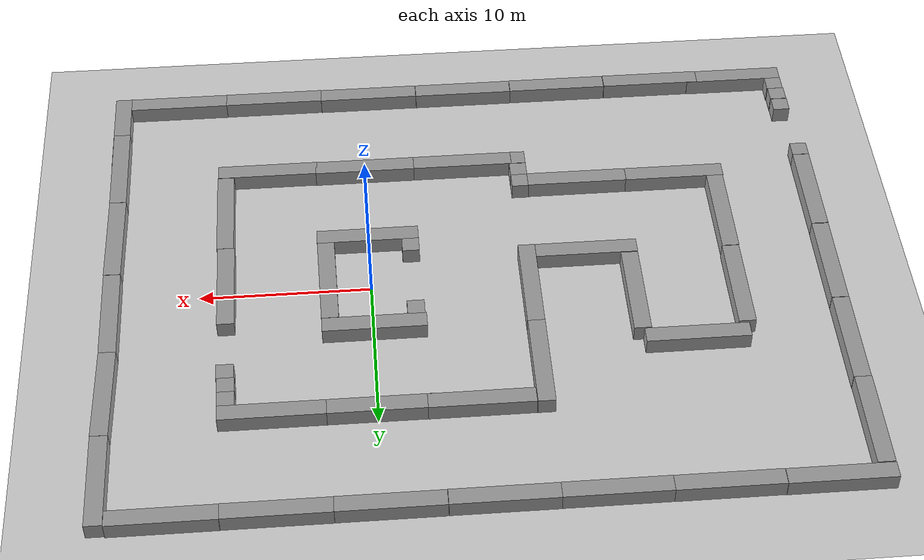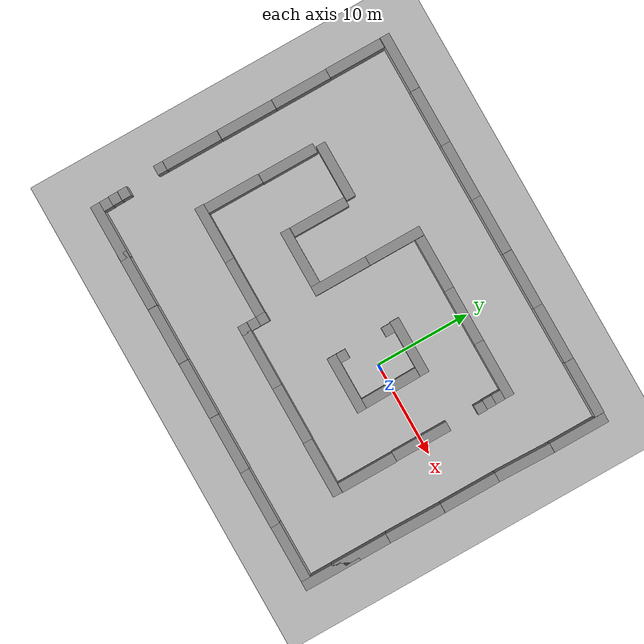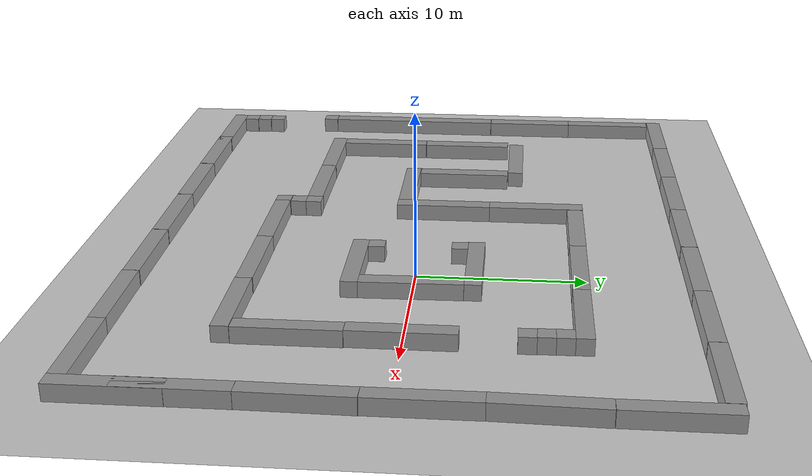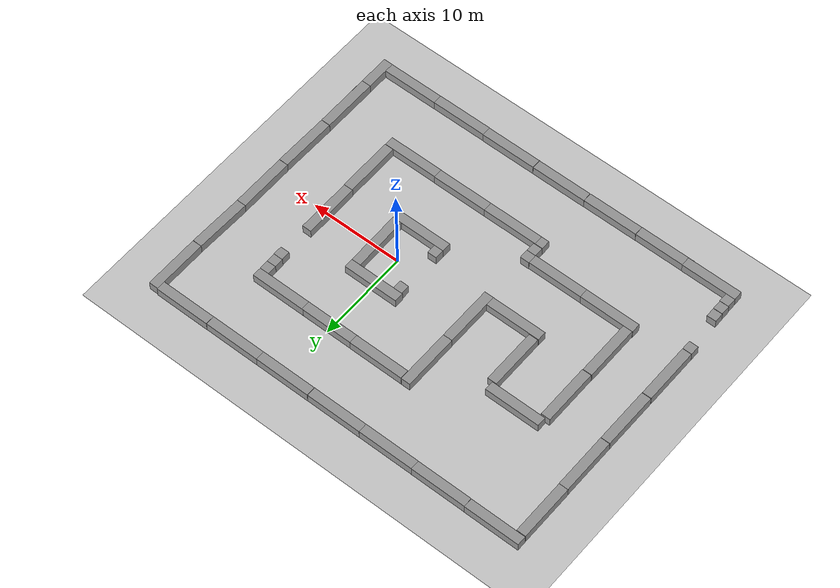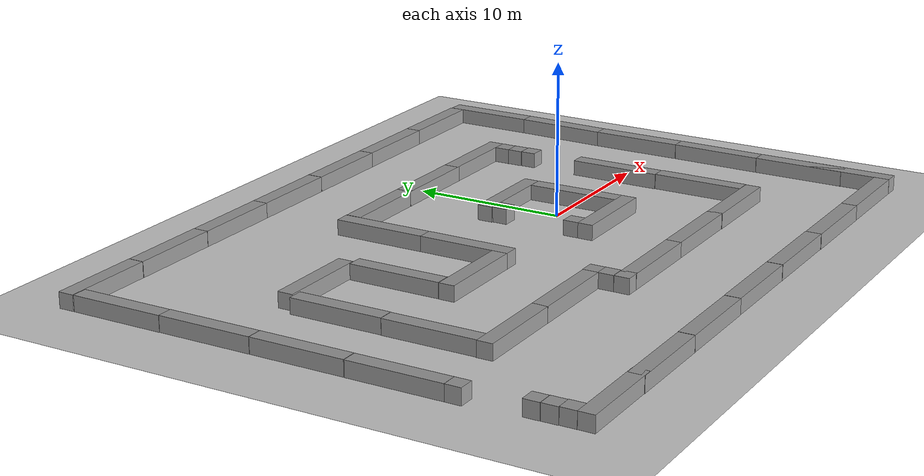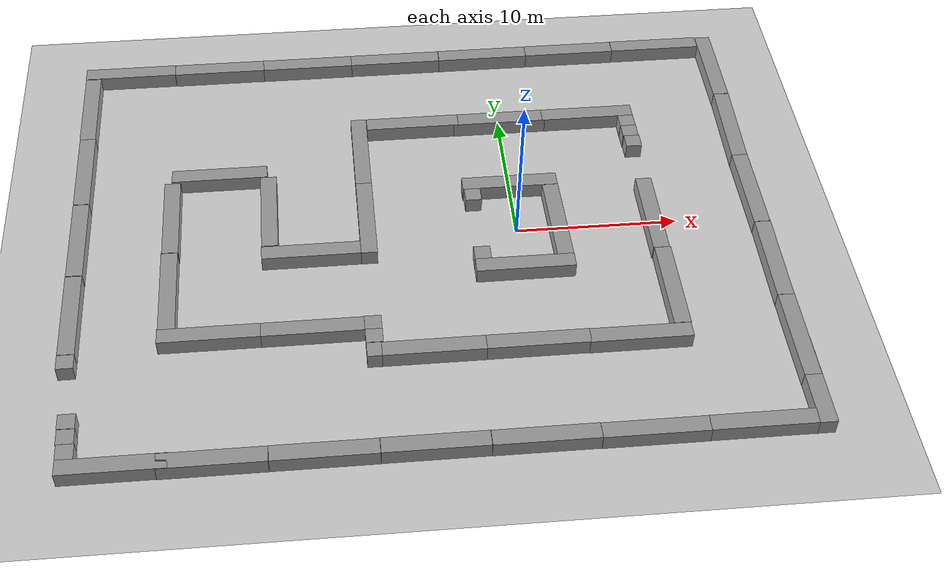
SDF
<sdf version="1.6">
 <world name="default">
  <light name="sun" type="directional">
   <pose>0 0 10 0 -0 0</pose>
   <diffuse>0.8 0.8 0.8 1</diffuse>
   <specular>0.2 0.2 0.2 1</specular>
   <attenuation>
    <range>1000</range>
    <constant>0.9</constant>
    <linear>0.01</linear>
    <quadratic>0.001</quadratic>
   </attenuation>
   <direction>-0.5 0.1 -0.9</direction>
  </light>
  <model name="ground_plane">
   <static>1</static>
   <link name="link">
    <collision name="collision">
     <geometry><plane><normal>0 0 1</normal><size>100 100</size></plane></geometry>
     <surface>
      <contact><collide_bitmask>65535</collide_bitmask></contact>
      <friction><ode><mu>100</mu><mu2>50</mu2></ode></friction>
     </surface>
    </collision>
    <visual name="visual">
     <cast_shadows>0</cast_shadows>
     <geometry><plane><normal>0 0 1</normal><size>100 100</size></plane></geometry>
     <material>
      <script><uri>file://media/materials/scripts/gazebo.material</uri><name>Gazebo/Grey</name></script>
     </material>
    </visual>
   </link>
  </model>
  <gravity>0 0 -9.8</gravity>
  <magnetic_field>6e-06 2.3e-05 -4.2e-05</magnetic_field>
  <atmosphere type="adiabatic"/>
  <physics name="default_physics" default="0" type="ode">
   <max_step_size>0.001</max_step_size>
   <real_time_factor>1</real_time_factor>
   <real_time_update_rate>1000</real_time_update_rate>
  </physics>
  <scene><ambient>0.4 0.4 0.4 1</ambient><background>0.7 0.7 0.7 1</background><shadows>1</shadows></scene>
  <audio><device>default</device></audio>
  <spherical_coordinates>
   <surface_model>EARTH_WGS84</surface_model>
   <latitude_deg>0</latitude_deg>
   <longitude_deg>0</longitude_deg>
   <elevation>0</elevation>
   <heading_deg>0</heading_deg>
  </spherical_coordinates>
  <model name="long_wall">
   <link name="link">
    <inertial>
     <mass>1</mass>
     <inertia>
      <ixx>0.166667</ixx>
      <ixy>0</ixy>
      <ixz>0</ixz>
      <iyy>0.166667</iyy>
      <iyz>0</iyz>
      <izz>0.166667</izz>
     </inertia>
    </inertial>
    <visual name="visual">
     <geometry><box><size>6 1 1</size></box></geometry>
     <material>
      <script><name>Gazebo/Grey</name><uri>file://media/materials/scripts/gazebo.material</uri></script>
      <shader type="vertex"><normal_map>__default__</normal_map></shader>
      <ambient>0.3 0.3 0.3 1</ambient>
      <diffuse>0.7 0.7 0.7 1</diffuse>
      <specular>0.01 0.01 0.01 1</specular>
      <emissive>0 0 0 1</emissive>
     </material>
    </visual>
    <collision name="collision">
     <geometry><box><size>1 1 1</size></box></geometry>
     <surface>
      <friction>
       <ode><mu>1</mu><mu2>1</mu2><fdir1>0 0 0</fdir1><slip1>0</slip1><slip2>0</slip2></ode>
       <torsional>
        <coefficient>1</coefficient>
        <patch_radius>0</patch_radius>
        <surface_radius>0</surface_radius>
        <use_patch_radius>1</use_patch_radius>
        <ode><slip>0</slip></ode>
       </torsional>
      </friction>
      <bounce><restitution_coefficient>0</restitution_coefficient><threshold>1e+06</threshold></bounce>
      <contact>
       <collide_without_contact>0</collide_without_contact>
       <collide_without_contact_bitmask>1</collide_without_contact_bitmask>
       <collide_bitmask>1</collide_bitmask>
       <ode>
        <soft_cfm>0</soft_cfm>
        <soft_erp>0.2</soft_erp>
        <kp>1e+13</kp>
        <kd>1</kd>
        <max_vel>0.01</max_vel>
        <min_depth>0</min_depth>
       </ode>
       <bullet>
        <split_impulse>1</split_impulse>
        <split_impulse_penetration_threshold>-0.01</split_impulse_penetration_threshold>
        <soft_cfm>0</soft_cfm>
        <soft_erp>0.2</soft_erp>
        <kp>1e+13</kp>
        <kd>1</kd>
       </bullet>
      </contact>
     </surface>
    </collision>
   </link>
   <static>0</static>
   <pose>0.049255 -3.53236 0.5 0 -0 0</pose>
  </model>
  <model name="long_wall_0">
   <link name="link">
    <inertial>
     <mass>1</mass>
     <inertia>
      <ixx>0.166667</ixx>
      <ixy>0</ixy>
      <ixz>0</ixz>
      <iyy>0.166667</iyy>
      <iyz>0</iyz>
      <izz>0.166667</izz>
     </inertia>
    </inertial>
    <visual name="visual">
     <geometry><box><size>6 1 1</size></box></geometry>
     <material>
      <script><name>Gazebo/Grey</name><uri>file://media/materials/scripts/gazebo.material</uri></script>
      <shader type="vertex"><normal_map>__default__</normal_map></shader>
      <ambient>0.3 0.3 0.3 1</ambient>
      <diffuse>0.7 0.7 0.7 1</diffuse>
      <specular>0.01 0.01 0.01 1</specular>
      <emissive>0 0 0 1</emissive>
     </material>
     <pose>0 0 0.5 0 -0 0</pose>
    </visual>
    <collision name="collision">
     <geometry><box><size>1 1 1</size></box></geometry>
     <surface>
      <friction>
       <ode><mu>1</mu><mu2>1</mu2><fdir1>0 0 0</fdir1><slip1>0</slip1><slip2>0</slip2></ode>
       <torsional>
        <coefficient>1</coefficient>
        <patch_radius>0</patch_radius>
        <surface_radius>0</surface_radius>
        <use_patch_radius>1</use_patch_radius>
        <ode><slip>0</slip></ode>
       </torsional>
      </friction>
      <bounce><restitution_coefficient>0</restitution_coefficient><threshold>1e+06</threshold></bounce>
      <contact>
       <collide_without_contact>0</collide_without_contact>
       <collide_without_contact_bitmask>1</collide_without_contact_bitmask>
       <collide_bitmask>1</collide_bitmask>
       <ode>
        <soft_cfm>0</soft_cfm>
        <soft_erp>0.2</soft_erp>
        <kp>1e+13</kp>
        <kd>1</kd>
        <max_vel>0.01</max_vel>
        <min_depth>0</min_depth>
       </ode>
       <bullet>
        <split_impulse>1</split_impulse>
        <split_impulse_penetration_threshold>-0.01</split_impulse_penetration_threshold>
        <soft_cfm>0</soft_cfm>
        <soft_erp>0.2</soft_erp>
        <kp>1e+13</kp>
        <kd>1</kd>
       </bullet>
      </contact>
     </surface>
    </collision>
   </link>
   <static>0</static>
   <pose>2.49568 -0.041218 0 0 0 -1.55477</pose>
  </model>
  <model name="long_wall_0_0">
   <link name="link">
    <inertial>
     <mass>1</mass>
     <inertia>
      <ixx>0.166667</ixx>
      <ixy>0</ixy>
      <ixz>0</ixz>
      <iyy>0.166667</iyy>
      <iyz>0</iyz>
      <izz>0.166667</izz>
     </inertia>
    </inertial>
    <visual name="visual">
     <geometry><box><size>6 1 1</size></box></geometry>
     <material>
      <script><name>Gazebo/Grey</name><uri>file://media/materials/scripts/gazebo.material</uri></script>
      <shader type="vertex"><normal_map>__default__</normal_map></shader>
      <ambient>0.3 0.3 0.3 1</ambient>
      <diffuse>0.7 0.7 0.7 1</diffuse>
      <specular>0.01 0.01 0.01 1</specular>
      <emissive>0 0 0 1</emissive>
     </material>
     <pose>0 0 0.5 0 -0 0</pose>
    </visual>
    <collision name="collision">
     <geometry><box><size>1 1 1</size></box></geometry>
     <surface>
      <friction>
       <ode><mu>1</mu><mu2>1</mu2><fdir1>0 0 0</fdir1><slip1>0</slip1><slip2>0</slip2></ode>
       <torsional>
        <coefficient>1</coefficient>
        <patch_radius>0</patch_radius>
        <surface_radius>0</surface_radius>
        <use_patch_radius>1</use_patch_radius>
        <ode><slip>0</slip></ode>
       </torsional>
      </friction>
      <bounce><restitution_coefficient>0</restitution_coefficient><threshold>1e+06</threshold></bounce>
      <contact>
       <collide_without_contact>0</collide_without_contact>
       <collide_without_contact_bitmask>1</collide_without_contact_bitmask>
       <collide_bitmask>1</collide_bitmask>
       <ode>
        <soft_cfm>0</soft_cfm>
        <soft_erp>0.2</soft_erp>
        <kp>1e+13</kp>
        <kd>1</kd>
        <max_vel>0.01</max_vel>
        <min_depth>0</min_depth>
       </ode>
       <bullet>
        <split_impulse>1</split_impulse>
        <split_impulse_penetration_threshold>-0.01</split_impulse_penetration_threshold>
        <soft_cfm>0</soft_cfm>
        <soft_erp>0.2</soft_erp>
        <kp>1e+13</kp>
        <kd>1</kd>
       </bullet>
      </contact>
     </surface>
    </collision>
   </link>
   <static>0</static>
   <pose>-0.064351 3.46733 0 0 -0 0</pose>
  </model>
  <model name="unit_box">
   <pose>-2.45124 -2.53302 0.5 0 -0 0</pose>
   <link name="link">
    <inertial>
     <mass>1</mass>
     <inertia>
      <ixx>0.166667</ixx>
      <ixy>0</ixy>
      <ixz>0</ixz>
      <iyy>0.166667</iyy>
      <iyz>0</iyz>
      <izz>0.166667</izz>
     </inertia>
    </inertial>
    <collision name="collision"><geometry><box><size>1 1 1</size></box></geometry></collision>
    <visual name="visual">
     <geometry><box><size>1 1 1</size></box></geometry>
     <material>
      <script><name>Gazebo/Grey</name><uri>file://media/materials/scripts/gazebo.material</uri></script>
     </material>
    </visual>
   </link>
  </model>
  <model name="unit_box_0">
   <pose>-2.48602 2.47883 0.5 0 -0 0</pose>
   <link name="link">
    <inertial>
     <mass>1</mass>
     <inertia>
      <ixx>0.166667</ixx>
      <ixy>0</ixy>
      <ixz>0</ixz>
      <iyy>0.166667</iyy>
      <iyz>0</iyz>
      <izz>0.166667</izz>
     </inertia>
    </inertial>
    <collision name="collision"><geometry><box><size>1 1 1</size></box></geometry></collision>
    <visual name="visual">
     <geometry><box><size>1 1 1</size></box></geometry>
     <material>
      <script><name>Gazebo/Grey</name><uri>file://media/materials/scripts/gazebo.material</uri></script>
     </material>
    </visual>
   </link>
  </model>
  <model name="long_wall_0_1">
   <link name="link">
    <inertial>
     <mass>1</mass>
     <inertia>
      <ixx>0.166667</ixx>
      <ixy>0</ixy>
      <ixz>0</ixz>
      <iyy>0.166667</iyy>
      <iyz>0</iyz>
      <izz>0.166667</izz>
     </inertia>
    </inertial>
    <visual name="visual">
     <geometry><box><size>6 1 1</size></box></geometry>
     <material>
      <script><name>Gazebo/Grey</name><uri>file://media/materials/scripts/gazebo.material</uri></script>
      <shader type="vertex"><normal_map>__default__</normal_map></shader>
      <ambient>0.3 0.3 0.3 1</ambient>
      <diffuse>0.7 0.7 0.7 1</diffuse>
      <specular>0.01 0.01 0.01 1</specular>
      <emissive>0 0 0 1</emissive>
     </material>
     <pose>0 0 0.5 0 -0 0</pose>
    </visual>
    <collision name="collision">
     <geometry><box><size>1 1 1</size></box></geometry>
     <surface>
      <friction>
       <ode><mu>1</mu><mu2>1</mu2><fdir1>0 0 0</fdir1><slip1>0</slip1><slip2>0</slip2></ode>
       <torsional>
        <coefficient>1</coefficient>
        <patch_radius>0</patch_radius>
        <surface_radius>0</surface_radius>
        <use_patch_radius>1</use_patch_radius>
        <ode><slip>0</slip></ode>
       </torsional>
      </friction>
      <bounce><restitution_coefficient>0</restitution_coefficient><threshold>1e+06</threshold></bounce>
      <contact>
       <collide_without_contact>0</collide_without_contact>
       <collide_without_contact_bitmask>1</collide_without_contact_bitmask>
       <collide_bitmask>1</collide_bitmask>
       <ode>
        <soft_cfm>0</soft_cfm>
        <soft_erp>0.2</soft_erp>
        <kp>1e+13</kp>
        <kd>1</kd>
        <max_vel>0.01</max_vel>
        <min_depth>0</min_depth>
       </ode>
       <bullet>
        <split_impulse>1</split_impulse>
        <split_impulse_penetration_threshold>-0.01</split_impulse_penetration_threshold>
        <soft_cfm>0</soft_cfm>
        <soft_erp>0.2</soft_erp>
        <kp>1e+13</kp>
        <kd>1</kd>
       </bullet>
      </contact>
     </surface>
    </collision>
   </link>
   <static>0</static>
   <pose>-0.009202 -9.5091 0 0 -0 0</pose>
  </model>
  <model name="long_wall_0_2">
   <link name="link">
    <inertial>
     <mass>1</mass>
     <inertia>
      <ixx>0.166667</ixx>
      <ixy>0</ixy>
      <ixz>0</ixz>
      <iyy>0.166667</iyy>
      <iyz>0</iyz>
      <izz>0.166667</izz>
     </inertia>
    </inertial>
    <visual name="visual">
     <geometry><box><size>6 1 1</size></box></geometry>
     <material>
      <script><name>Gazebo/Grey</name><uri>file://media/materials/scripts/gazebo.material</uri></script>
      <shader type="vertex"><normal_map>__default__</normal_map></shader>
      <ambient>0.3 0.3 0.3 1</ambient>
      <diffuse>0.7 0.7 0.7 1</diffuse>
      <specular>0.01 0.01 0.01 1</specular>
      <emissive>0 0 0 1</emissive>
     </material>
     <pose>0 0 0.5 0 -0 0</pose>
    </visual>
    <collision name="collision">
     <geometry><box><size>1 1 1</size></box></geometry>
     <surface>
      <friction>
       <ode><mu>1</mu><mu2>1</mu2><fdir1>0 0 0</fdir1><slip1>0</slip1><slip2>0</slip2></ode>
       <torsional>
        <coefficient>1</coefficient>
        <patch_radius>0</patch_radius>
        <surface_radius>0</surface_radius>
        <use_patch_radius>1</use_patch_radius>
        <ode><slip>0</slip></ode>
       </torsional>
      </friction>
      <bounce><restitution_coefficient>0</restitution_coefficient><threshold>1e+06</threshold></bounce>
      <contact>
       <collide_without_contact>0</collide_without_contact>
       <collide_without_contact_bitmask>1</collide_without_contact_bitmask>
       <collide_bitmask>1</collide_bitmask>
       <ode>
        <soft_cfm>0</soft_cfm>
        <soft_erp>0.2</soft_erp>
        <kp>1e+13</kp>
        <kd>1</kd>
        <max_vel>0.01</max_vel>
        <min_depth>0</min_depth>
       </ode>
       <bullet>
        <split_impulse>1</split_impulse>
        <split_impulse_penetration_threshold>-0.01</split_impulse_penetration_threshold>
        <soft_cfm>0</soft_cfm>
        <soft_erp>0.2</soft_erp>
        <kp>1e+13</kp>
        <kd>1</kd>
       </bullet>
      </contact>
     </surface>
    </collision>
   </link>
   <static>0</static>
   <pose>-0.017464 9.51056 0 0 -0 0</pose>
  </model>
  <model name="long_wall_0_3">
   <link name="link">
    <inertial>
     <mass>1</mass>
     <inertia>
      <ixx>0.166667</ixx>
      <ixy>0</ixy>
      <ixz>0</ixz>
      <iyy>0.166667</iyy>
      <iyz>0</iyz>
      <izz>0.166667</izz>
     </inertia>
    </inertial>
    <visual name="visual">
     <geometry><box><size>6 1 1</size></box></geometry>
     <material>
      <script><name>Gazebo/Grey</name><uri>file://media/materials/scripts/gazebo.material</uri></script>
      <shader type="vertex"><normal_map>__default__</normal_map></shader>
      <ambient>0.3 0.3 0.3 1</ambient>
      <diffuse>0.7 0.7 0.7 1</diffuse>
      <specular>0.01 0.01 0.01 1</specular>
      <emissive>0 0 0 1</emissive>
     </material>
     <pose>0 0 0.5 0 -0 0</pose>
    </visual>
    <collision name="collision">
     <geometry><box><size>1 1 1</size></box></geometry>
     <surface>
      <friction>
       <ode><mu>1</mu><mu2>1</mu2><fdir1>0 0 0</fdir1><slip1>0</slip1><slip2>0</slip2></ode>
       <torsional>
        <coefficient>1</coefficient>
        <patch_radius>0</patch_radius>
        <surface_radius>0</surface_radius>
        <use_patch_radius>1</use_patch_radius>
        <ode><slip>0</slip></ode>
       </torsional>
      </friction>
      <bounce><restitution_coefficient>0</restitution_coefficient><threshold>1e+06</threshold></bounce>
      <contact>
       <collide_without_contact>0</collide_without_contact>
       <collide_without_contact_bitmask>1</collide_without_contact_bitmask>
       <collide_bitmask>1</collide_bitmask>
       <ode>
        <soft_cfm>0</soft_cfm>
        <soft_erp>0.2</soft_erp>
        <kp>1e+13</kp>
        <kd>1</kd>
        <max_vel>0.01</max_vel>
        <min_depth>0</min_depth>
       </ode>
       <bullet>
        <split_impulse>1</split_impulse>
        <split_impulse_penetration_threshold>-0.01</split_impulse_penetration_threshold>
        <soft_cfm>0</soft_cfm>
        <soft_erp>0.2</soft_erp>
        <kp>1e+13</kp>
        <kd>1</kd>
       </bullet>
      </contact>
     </surface>
    </collision>
   </link>
   <static>0</static>
   <pose>5.92003 -9.53571 0 0 -0 0</pose>
  </model>
  <model name="long_wall_0_4">
   <link name="link">
    <inertial>
     <mass>1</mass>
     <inertia>
      <ixx>0.166667</ixx>
      <ixy>0</ixy>
      <ixz>0</ixz>
      <iyy>0.166667</iyy>
      <iyz>0</iyz>
      <izz>0.166667</izz>
     </inertia>
    </inertial>
    <visual name="visual">
     <geometry><box><size>6 1 1</size></box></geometry>
     <material>
      <script><name>Gazebo/Grey</name><uri>file://media/materials/scripts/gazebo.material</uri></script>
      <shader type="vertex"><normal_map>__default__</normal_map></shader>
      <ambient>0.3 0.3 0.3 1</ambient>
      <diffuse>0.7 0.7 0.7 1</diffuse>
      <specular>0.01 0.01 0.01 1</specular>
      <emissive>0 0 0 1</emissive>
     </material>
     <pose>0 0 0.5 0 -0 0</pose>
    </visual>
    <collision name="collision">
     <geometry><box><size>1 1 1</size></box></geometry>
     <surface>
      <friction>
       <ode><mu>1</mu><mu2>1</mu2><fdir1>0 0 0</fdir1><slip1>0</slip1><slip2>0</slip2></ode>
       <torsional>
        <coefficient>1</coefficient>
        <patch_radius>0</patch_radius>
        <surface_radius>0</surface_radius>
        <use_patch_radius>1</use_patch_radius>
        <ode><slip>0</slip></ode>
       </torsional>
      </friction>
      <bounce><restitution_coefficient>0</restitution_coefficient><threshold>1e+06</threshold></bounce>
      <contact>
       <collide_without_contact>0</collide_without_contact>
       <collide_without_contact_bitmask>1</collide_without_contact_bitmask>
       <collide_bitmask>1</collide_bitmask>
       <ode>
        <soft_cfm>0</soft_cfm>
        <soft_erp>0.2</soft_erp>
        <kp>1e+13</kp>
        <kd>1</kd>
        <max_vel>0.01</max_vel>
        <min_depth>0</min_depth>
       </ode>
       <bullet>
        <split_impulse>1</split_impulse>
        <split_impulse_penetration_threshold>-0.01</split_impulse_penetration_threshold>
        <soft_cfm>0</soft_cfm>
        <soft_erp>0.2</soft_erp>
        <kp>1e+13</kp>
        <kd>1</kd>
       </bullet>
      </contact>
     </surface>
    </collision>
   </link>
   <static>0</static>
   <pose>5.83103 9.51107 0 0 -0 0</pose>
  </model>
  <model name="long_wall_0_5">
   <link name="link">
    <inertial>
     <mass>1</mass>
     <inertia>
      <ixx>0.166667</ixx>
      <ixy>0</ixy>
      <ixz>0</ixz>
      <iyy>0.166667</iyy>
      <iyz>0</iyz>
      <izz>0.166667</izz>
     </inertia>
    </inertial>
    <visual name="visual">
     <geometry><box><size>6 1 1</size></box></geometry>
     <material>
      <script><name>Gazebo/Grey</name><uri>file://media/materials/scripts/gazebo.material</uri></script>
      <shader type="vertex"><normal_map>__default__</normal_map></shader>
      <ambient>0.3 0.3 0.3 1</ambient>
      <diffuse>0.7 0.7 0.7 1</diffuse>
      <specular>0.01 0.01 0.01 1</specular>
      <emissive>0 0 0 1</emissive>
     </material>
     <pose>0 0 0.5 0 -0 0</pose>
    </visual>
    <collision name="collision">
     <geometry><box><size>1 1 1</size></box></geometry>
     <surface>
      <friction>
       <ode><mu>1</mu><mu2>1</mu2><fdir1>0 0 0</fdir1><slip1>0</slip1><slip2>0</slip2></ode>
       <torsional>
        <coefficient>1</coefficient>
        <patch_radius>0</patch_radius>
        <surface_radius>0</surface_radius>
        <use_patch_radius>1</use_patch_radius>
        <ode><slip>0</slip></ode>
       </torsional>
      </friction>
      <bounce><restitution_coefficient>0</restitution_coefficient><threshold>1e+06</threshold></bounce>
      <contact>
       <collide_without_contact>0</collide_without_contact>
       <collide_without_contact_bitmask>1</collide_without_contact_bitmask>
       <collide_bitmask>1</collide_bitmask>
       <ode>
        <soft_cfm>0</soft_cfm>
        <soft_erp>0.2</soft_erp>
        <kp>1e+13</kp>
        <kd>1</kd>
        <max_vel>0.01</max_vel>
        <min_depth>0</min_depth>
       </ode>
       <bullet>
        <split_impulse>1</split_impulse>
        <split_impulse_penetration_threshold>-0.01</split_impulse_penetration_threshold>
        <soft_cfm>0</soft_cfm>
        <soft_erp>0.2</soft_erp>
        <kp>1e+13</kp>
        <kd>1</kd>
       </bullet>
      </contact>
     </surface>
    </collision>
   </link>
   <static>0</static>
   <pose>8.45903 -6.01437 0 0 -0 1.5708</pose>
  </model>
  <model name="long_wall_0_6">
   <link name="link">
    <inertial>
     <mass>1</mass>
     <inertia>
      <ixx>0.166667</ixx>
      <ixy>0</ixy>
      <ixz>0</ixz>
      <iyy>0.166667</iyy>
      <iyz>0</iyz>
      <izz>0.166667</izz>
     </inertia>
    </inertial>
    <visual name="visual">
     <geometry><box><size>6 1 1</size></box></geometry>
     <material>
      <script><name>Gazebo/Grey</name><uri>file://media/materials/scripts/gazebo.material</uri></script>
      <shader type="vertex"><normal_map>__default__</normal_map></shader>
      <ambient>0.3 0.3 0.3 1</ambient>
      <diffuse>0.7 0.7 0.7 1</diffuse>
      <specular>0.01 0.01 0.01 1</specular>
      <emissive>0 0 0 1</emissive>
     </material>
     <pose>0 0 0.5 0 -0 0</pose>
    </visual>
    <collision name="collision">
     <geometry><box><size>1 1 1</size></box></geometry>
     <surface>
      <friction>
       <ode><mu>1</mu><mu2>1</mu2><fdir1>0 0 0</fdir1><slip1>0</slip1><slip2>0</slip2></ode>
       <torsional>
        <coefficient>1</coefficient>
        <patch_radius>0</patch_radius>
        <surface_radius>0</surface_radius>
        <use_patch_radius>1</use_patch_radius>
        <ode><slip>0</slip></ode>
       </torsional>
      </friction>
      <bounce><restitution_coefficient>0</restitution_coefficient><threshold>1e+06</threshold></bounce>
      <contact>
       <collide_without_contact>0</collide_without_contact>
       <collide_without_contact_bitmask>1</collide_without_contact_bitmask>
       <collide_bitmask>1</collide_bitmask>
       <ode>
        <soft_cfm>0</soft_cfm>
        <soft_erp>0.2</soft_erp>
        <kp>1e+13</kp>
        <kd>1</kd>
        <max_vel>0.01</max_vel>
        <min_depth>0</min_depth>
       </ode>
       <bullet>
        <split_impulse>1</split_impulse>
        <split_impulse_penetration_threshold>-0.01</split_impulse_penetration_threshold>
        <soft_cfm>0</soft_cfm>
        <soft_erp>0.2</soft_erp>
        <kp>1e+13</kp>
        <kd>1</kd>
       </bullet>
      </contact>
     </surface>
    </collision>
   </link>
   <static>0</static>
   <pose>8.40487 -0.007823 0 0 0 -1.5708</pose>
  </model>
  <model name="unit_box_1">
   <pose>8.34651 8.51743 0.5 0 -0 0</pose>
   <link name="link">
    <inertial>
     <mass>1</mass>
     <inertia>
      <ixx>0.166667</ixx>
      <ixy>0</ixy>
      <ixz>0</ixz>
      <iyy>0.166667</iyy>
      <iyz>0</iyz>
      <izz>0.166667</izz>
     </inertia>
    </inertial>
    <collision name="collision"><geometry><box><size>1 1 1</size></box></geometry></collision>
    <visual name="visual">
     <geometry><box><size>1 1 1</size></box></geometry>
     <material>
      <script><name>Gazebo/Grey</name><uri>file://media/materials/scripts/gazebo.material</uri></script>
     </material>
    </visual>
   </link>
  </model>
  <model name="unit_box_2">
   <pose>8.36219 7.52912 0.5 0 -0 0</pose>
   <link name="link">
    <inertial>
     <mass>1</mass>
     <inertia>
      <ixx>0.166667</ixx>
      <ixy>0</ixy>
      <ixz>0</ixz>
      <iyy>0.166667</iyy>
      <iyz>0</iyz>
      <izz>0.166667</izz>
     </inertia>
    </inertial>
    <collision name="collision"><geometry><box><size>1 1 1</size></box></geometry></collision>
    <visual name="visual">
     <geometry><box><size>1 1 1</size></box></geometry>
     <material>
      <script><name>Gazebo/Grey</name><uri>file://media/materials/scripts/gazebo.material</uri></script>
     </material>
    </visual>
   </link>
  </model>
  <model name="unit_box_3">
   <pose>8.4049 6.54082 0.5 0 -0 0</pose>
   <link name="link">
    <inertial>
     <mass>1</mass>
     <inertia>
      <ixx>0.166667</ixx>
      <ixy>0</ixy>
      <ixz>0</ixz>
      <iyy>0.166667</iyy>
      <iyz>0</iyz>
      <izz>0.166667</izz>
     </inertia>
    </inertial>
    <collision name="collision"><geometry><box><size>1 1 1</size></box></geometry></collision>
    <visual name="visual">
     <geometry><box><size>1 1 1</size></box></geometry>
     <material>
      <script><name>Gazebo/Grey</name><uri>file://media/materials/scripts/gazebo.material</uri></script>
     </material>
    </visual>
   </link>
  </model>
  <model name="long_wall_0_7">
   <link name="link">
    <inertial>
     <mass>1</mass>
     <inertia>
      <ixx>0.166667</ixx>
      <ixy>0</ixy>
      <ixz>0</ixz>
      <iyy>0.166667</iyy>
      <iyz>0</iyz>
      <izz>0.166667</izz>
     </inertia>
    </inertial>
    <visual name="visual">
     <geometry><box><size>6 1 1</size></box></geometry>
     <material>
      <script><name>Gazebo/Grey</name><uri>file://media/materials/scripts/gazebo.material</uri></script>
      <shader type="vertex"><normal_map>__default__</normal_map></shader>
      <ambient>0.3 0.3 0.3 1</ambient>
      <diffuse>0.7 0.7 0.7 1</diffuse>
      <specular>0.01 0.01 0.01 1</specular>
      <emissive>0 0 0 1</emissive>
     </material>
     <pose>0 0 0.5 0 -0 0</pose>
    </visual>
    <collision name="collision">
     <geometry><box><size>1 1 1</size></box></geometry>
     <surface>
      <friction>
       <ode><mu>1</mu><mu2>1</mu2><fdir1>0 0 0</fdir1><slip1>0</slip1><slip2>0</slip2></ode>
       <torsional>
        <coefficient>1</coefficient>
        <patch_radius>0</patch_radius>
        <surface_radius>0</surface_radius>
        <use_patch_radius>1</use_patch_radius>
        <ode><slip>0</slip></ode>
       </torsional>
      </friction>
      <bounce><restitution_coefficient>0</restitution_coefficient><threshold>1e+06</threshold></bounce>
      <contact>
       <collide_without_contact>0</collide_without_contact>
       <collide_without_contact_bitmask>1</collide_without_contact_bitmask>
       <collide_bitmask>1</collide_bitmask>
       <ode>
        <soft_cfm>0</soft_cfm>
        <soft_erp>0.2</soft_erp>
        <kp>1e+13</kp>
        <kd>1</kd>
        <max_vel>0.01</max_vel>
        <min_depth>0</min_depth>
       </ode>
       <bullet>
        <split_impulse>1</split_impulse>
        <split_impulse_penetration_threshold>-0.01</split_impulse_penetration_threshold>
        <soft_cfm>0</soft_cfm>
        <soft_erp>0.2</soft_erp>
        <kp>1e+13</kp>
        <kd>1</kd>
       </bullet>
      </contact>
     </surface>
    </collision>
   </link>
   <static>0</static>
   <pose>-5.72862 9.522 0 0 -0 0</pose>
  </model>
  <model name="long_wall_0_8">
   <link name="link">
    <inertial>
     <mass>1</mass>
     <inertia>
      <ixx>0.166667</ixx>
      <ixy>0</ixy>
      <ixz>0</ixz>
      <iyy>0.166667</iyy>
      <iyz>0</iyz>
      <izz>0.166667</izz>
     </inertia>
    </inertial>
    <visual name="visual">
     <geometry><box><size>6 1 1</size></box></geometry>
     <material>
      <script><name>Gazebo/Grey</name><uri>file://media/materials/scripts/gazebo.material</uri></script>
      <shader type="vertex"><normal_map>__default__</normal_map></shader>
      <ambient>0.3 0.3 0.3 1</ambient>
      <diffuse>0.7 0.7 0.7 1</diffuse>
      <specular>0.01 0.01 0.01 1</specular>
      <emissive>0 0 0 1</emissive>
     </material>
     <pose>0 0 0.5 0 -0 0</pose>
    </visual>
    <collision name="collision">
     <geometry><box><size>1 1 1</size></box></geometry>
     <surface>
      <friction>
       <ode><mu>1</mu><mu2>1</mu2><fdir1>0 0 0</fdir1><slip1>0</slip1><slip2>0</slip2></ode>
       <torsional>
        <coefficient>1</coefficient>
        <patch_radius>0</patch_radius>
        <surface_radius>0</surface_radius>
        <use_patch_radius>1</use_patch_radius>
        <ode><slip>0</slip></ode>
       </torsional>
      </friction>
      <bounce><restitution_coefficient>0</restitution_coefficient><threshold>1e+06</threshold></bounce>
      <contact>
       <collide_without_contact>0</collide_without_contact>
       <collide_without_contact_bitmask>1</collide_without_contact_bitmask>
       <collide_bitmask>1</collide_bitmask>
       <ode>
        <soft_cfm>0</soft_cfm>
        <soft_erp>0.2</soft_erp>
        <kp>1e+13</kp>
        <kd>1</kd>
        <max_vel>0.01</max_vel>
        <min_depth>0</min_depth>
       </ode>
       <bullet>
        <split_impulse>1</split_impulse>
        <split_impulse_penetration_threshold>-0.01</split_impulse_penetration_threshold>
        <soft_cfm>0</soft_cfm>
        <soft_erp>0.2</soft_erp>
        <kp>1e+13</kp>
        <kd>1</kd>
       </bullet>
      </contact>
     </surface>
    </collision>
   </link>
   <static>0</static>
   <pose>-6.007 -9.51284 0 0 -0 0</pose>
  </model>
  <model name="long_wall_0_9">
   <link name="link">
    <inertial>
     <mass>1</mass>
     <inertia>
      <ixx>0.166667</ixx>
      <ixy>0</ixy>
      <ixz>0</ixz>
      <iyy>0.166667</iyy>
      <iyz>0</iyz>
      <izz>0.166667</izz>
     </inertia>
    </inertial>
    <visual name="visual">
     <geometry><box><size>6 1 1</size></box></geometry>
     <material>
      <script><name>Gazebo/Grey</name><uri>file://media/materials/scripts/gazebo.material</uri></script>
      <shader type="vertex"><normal_map>__default__</normal_map></shader>
      <ambient>0.3 0.3 0.3 1</ambient>
      <diffuse>0.7 0.7 0.7 1</diffuse>
      <specular>0.01 0.01 0.01 1</specular>
      <emissive>0 0 0 1</emissive>
     </material>
     <pose>0 0 0.5 0 -0 0</pose>
    </visual>
    <collision name="collision">
     <geometry><box><size>1 1 1</size></box></geometry>
     <surface>
      <friction>
       <ode><mu>1</mu><mu2>1</mu2><fdir1>0 0 0</fdir1><slip1>0</slip1><slip2>0</slip2></ode>
       <torsional>
        <coefficient>1</coefficient>
        <patch_radius>0</patch_radius>
        <surface_radius>0</surface_radius>
        <use_patch_radius>1</use_patch_radius>
        <ode><slip>0</slip></ode>
       </torsional>
      </friction>
      <bounce><restitution_coefficient>0</restitution_coefficient><threshold>1e+06</threshold></bounce>
      <contact>
       <collide_without_contact>0</collide_without_contact>
       <collide_without_contact_bitmask>1</collide_without_contact_bitmask>
       <collide_bitmask>1</collide_bitmask>
       <ode>
        <soft_cfm>0</soft_cfm>
        <soft_erp>0.2</soft_erp>
        <kp>1e+13</kp>
        <kd>1</kd>
        <max_vel>0.01</max_vel>
        <min_depth>0</min_depth>
       </ode>
       <bullet>
        <split_impulse>1</split_impulse>
        <split_impulse_penetration_threshold>-0.01</split_impulse_penetration_threshold>
        <soft_cfm>0</soft_cfm>
        <soft_erp>0.2</soft_erp>
        <kp>1e+13</kp>
        <kd>1</kd>
       </bullet>
      </contact>
     </surface>
    </collision>
   </link>
   <static>0</static>
   <pose>-9.2589 7.02842 0 0 0 -1.5708</pose>
  </model>
  <model name="long_wall_0_10">
   <link name="link">
    <inertial>
     <mass>1</mass>
     <inertia>
      <ixx>0.166667</ixx>
      <ixy>0</ixy>
      <ixz>0</ixz>
      <iyy>0.166667</iyy>
      <iyz>0</iyz>
      <izz>0.166667</izz>
     </inertia>
    </inertial>
    <visual name="visual">
     <geometry><box><size>6 1 1</size></box></geometry>
     <material>
      <script><name>Gazebo/Grey</name><uri>file://media/materials/scripts/gazebo.material</uri></script>
      <shader type="vertex"><normal_map>__default__</normal_map></shader>
      <ambient>0.3 0.3 0.3 1</ambient>
      <diffuse>0.7 0.7 0.7 1</diffuse>
      <specular>0.01 0.01 0.01 1</specular>
      <emissive>0 0 0 1</emissive>
     </material>
     <pose>0 0 0.5 0 -0 0</pose>
    </visual>
    <collision name="collision">
     <geometry><box><size>1 1 1</size></box></geometry>
     <surface>
      <friction>
       <ode><mu>1</mu><mu2>1</mu2><fdir1>0 0 0</fdir1><slip1>0</slip1><slip2>0</slip2></ode>
       <torsional>
        <coefficient>1</coefficient>
        <patch_radius>0</patch_radius>
        <surface_radius>0</surface_radius>
        <use_patch_radius>1</use_patch_radius>
        <ode><slip>0</slip></ode>
       </torsional>
      </friction>
      <bounce><restitution_coefficient>0</restitution_coefficient><threshold>1e+06</threshold></bounce>
      <contact>
       <collide_without_contact>0</collide_without_contact>
       <collide_without_contact_bitmask>1</collide_without_contact_bitmask>
       <collide_bitmask>1</collide_bitmask>
       <ode>
        <soft_cfm>0</soft_cfm>
        <soft_erp>0.2</soft_erp>
        <kp>1e+13</kp>
        <kd>1</kd>
        <max_vel>0.01</max_vel>
        <min_depth>0</min_depth>
       </ode>
       <bullet>
        <split_impulse>1</split_impulse>
        <split_impulse_penetration_threshold>-0.01</split_impulse_penetration_threshold>
        <soft_cfm>0</soft_cfm>
        <soft_erp>0.2</soft_erp>
        <kp>1e+13</kp>
        <kd>1</kd>
       </bullet>
      </contact>
     </surface>
    </collision>
   </link>
   <static>0</static>
   <pose>-9.25333 1.037 0 0 0 -1.5708</pose>
  </model>
  <model name="unit_box_4">
   <pose>-9.37003 -9.50695 0.5 0 -0 0</pose>
   <link name="link">
    <inertial>
     <mass>1</mass>
     <inertia>
      <ixx>0.166667</ixx>
      <ixy>0</ixy>
      <ixz>0</ixz>
      <iyy>0.166667</iyy>
      <iyz>0</iyz>
      <izz>0.166667</izz>
     </inertia>
    </inertial>
    <collision name="collision"><geometry><box><size>1 1 1</size></box></geometry></collision>
    <visual name="visual">
     <geometry><box><size>1 1 1</size></box></geometry>
     <material>
      <script><name>Gazebo/Grey</name><uri>file://media/materials/scripts/gazebo.material</uri></script>
     </material>
    </visual>
   </link>
  </model>
  <model name="unit_box_5">
   <pose>-9.37382 -8.48354 0.5 0 -0 0</pose>
   <link name="link">
    <inertial>
     <mass>1</mass>
     <inertia>
      <ixx>0.166667</ixx>
      <ixy>0</ixy>
      <ixz>0</ixz>
      <iyy>0.166667</iyy>
      <iyz>0</iyz>
      <izz>0.166667</izz>
     </inertia>
    </inertial>
    <collision name="collision"><geometry><box><size>1 1 1</size></box></geometry></collision>
    <visual name="visual">
     <geometry><box><size>1 1 1</size></box></geometry>
     <material>
      <script><name>Gazebo/Grey</name><uri>file://media/materials/scripts/gazebo.material</uri></script>
     </material>
    </visual>
   </link>
  </model>
  <model name="unit_box_6">
   <pose>-9.3806 -7.48919 0.5 0 -0 0</pose>
   <link name="link">
    <inertial>
     <mass>1</mass>
     <inertia>
      <ixx>0.166667</ixx>
      <ixy>0</ixy>
      <ixz>0</ixz>
      <iyy>0.166667</iyy>
      <iyz>0</iyz>
      <izz>0.166667</izz>
     </inertia>
    </inertial>
    <collision name="collision"><geometry><box><size>1 1 1</size></box></geometry></collision>
    <visual name="visual">
     <geometry><box><size>1 1 1</size></box></geometry>
     <material>
      <script><name>Gazebo/Grey</name><uri>file://media/materials/scripts/gazebo.material</uri></script>
     </material>
    </visual>
   </link>
  </model>
  <model name="long_wall_0_11">
   <link name="link">
    <inertial>
     <mass>1</mass>
     <inertia>
      <ixx>0.166667</ixx>
      <ixy>0</ixy>
      <ixz>0</ixz>
      <iyy>0.166667</iyy>
      <iyz>0</iyz>
      <izz>0.166667</izz>
     </inertia>
    </inertial>
    <visual name="visual">
     <geometry><box><size>6 1 1</size></box></geometry>
     <material>
      <script><name>Gazebo/Grey</name><uri>file://media/materials/scripts/gazebo.material</uri></script>
      <shader type="vertex"><normal_map>__default__</normal_map></shader>
      <ambient>0.3 0.3 0.3 1</ambient>
      <diffuse>0.7 0.7 0.7 1</diffuse>
      <specular>0.01 0.01 0.01 1</specular>
      <emissive>0 0 0 1</emissive>
     </material>
     <pose>0 0 0.5 0 -0 0</pose>
    </visual>
    <collision name="collision">
     <geometry><box><size>1 1 1</size></box></geometry>
     <surface>
      <friction>
       <ode><mu>1</mu><mu2>1</mu2><fdir1>0 0 0</fdir1><slip1>0</slip1><slip2>0</slip2></ode>
       <torsional>
        <coefficient>1</coefficient>
        <patch_radius>0</patch_radius>
        <surface_radius>0</surface_radius>
        <use_patch_radius>1</use_patch_radius>
        <ode><slip>0</slip></ode>
       </torsional>
      </friction>
      <bounce><restitution_coefficient>0</restitution_coefficient><threshold>1e+06</threshold></bounce>
      <contact>
       <collide_without_contact>0</collide_without_contact>
       <collide_without_contact_bitmask>1</collide_without_contact_bitmask>
       <collide_bitmask>1</collide_bitmask>
       <ode>
        <soft_cfm>0</soft_cfm>
        <soft_erp>0.2</soft_erp>
        <kp>1e+13</kp>
        <kd>1</kd>
        <max_vel>0.01</max_vel>
        <min_depth>0</min_depth>
       </ode>
       <bullet>
        <split_impulse>1</split_impulse>
        <split_impulse_penetration_threshold>-0.01</split_impulse_penetration_threshold>
        <soft_cfm>0</soft_cfm>
        <soft_erp>0.2</soft_erp>
        <kp>1e+13</kp>
        <kd>1</kd>
       </bullet>
      </contact>
     </surface>
    </collision>
   </link>
   <static>0</static>
   <pose>-12.7536 -1.45734 0 0 -0 0</pose>
  </model>
  <model name="long_wall_0_12">
   <link name="link">
    <inertial>
     <mass>1</mass>
     <inertia>
      <ixx>0.166667</ixx>
      <ixy>0</ixy>
      <ixz>0</ixz>
      <iyy>0.166667</iyy>
      <iyz>0</iyz>
      <izz>0.166667</izz>
     </inertia>
    </inertial>
    <visual name="visual">
     <geometry><box><size>6 1 1</size></box></geometry>
     <material>
      <script><name>Gazebo/Grey</name><uri>file://media/materials/scripts/gazebo.material</uri></script>
      <shader type="vertex"><normal_map>__default__</normal_map></shader>
      <ambient>0.3 0.3 0.3 1</ambient>
      <diffuse>0.7 0.7 0.7 1</diffuse>
      <specular>0.01 0.01 0.01 1</specular>
      <emissive>0 0 0 1</emissive>
     </material>
     <pose>0 0 0.5 0 -0 0</pose>
    </visual>
    <collision name="collision">
     <geometry><box><size>1 1 1</size></box></geometry>
     <surface>
      <friction>
       <ode><mu>1</mu><mu2>1</mu2><fdir1>0 0 0</fdir1><slip1>0</slip1><slip2>0</slip2></ode>
       <torsional>
        <coefficient>1</coefficient>
        <patch_radius>0</patch_radius>
        <surface_radius>0</surface_radius>
        <use_patch_radius>1</use_patch_radius>
        <ode><slip>0</slip></ode>
       </torsional>
      </friction>
      <bounce><restitution_coefficient>0</restitution_coefficient><threshold>1e+06</threshold></bounce>
      <contact>
       <collide_without_contact>0</collide_without_contact>
       <collide_without_contact_bitmask>1</collide_without_contact_bitmask>
       <collide_bitmask>1</collide_bitmask>
       <ode>
        <soft_cfm>0</soft_cfm>
        <soft_erp>0.2</soft_erp>
        <kp>1e+13</kp>
        <kd>1</kd>
        <max_vel>0.01</max_vel>
        <min_depth>0</min_depth>
       </ode>
       <bullet>
        <split_impulse>1</split_impulse>
        <split_impulse_penetration_threshold>-0.01</split_impulse_penetration_threshold>
        <soft_cfm>0</soft_cfm>
        <soft_erp>0.2</soft_erp>
        <kp>1e+13</kp>
        <kd>1</kd>
       </bullet>
      </contact>
     </surface>
    </collision>
   </link>
   <static>0</static>
   <pose>-12.8634 -7.51779 0 0 -0 0</pose>
  </model>
  <model name="long_wall_0_13">
   <link name="link">
    <inertial>
     <mass>1</mass>
     <inertia>
      <ixx>0.166667</ixx>
      <ixy>0</ixy>
      <ixz>0</ixz>
      <iyy>0.166667</iyy>
      <iyz>0</iyz>
      <izz>0.166667</izz>
     </inertia>
    </inertial>
    <visual name="visual">
     <geometry><box><size>6 1 1</size></box></geometry>
     <material>
      <script><name>Gazebo/Grey</name><uri>file://media/materials/scripts/gazebo.material</uri></script>
      <shader type="vertex"><normal_map>__default__</normal_map></shader>
      <ambient>0.3 0.3 0.3 1</ambient>
      <diffuse>0.7 0.7 0.7 1</diffuse>
      <specular>0.01 0.01 0.01 1</specular>
      <emissive>0 0 0 1</emissive>
     </material>
     <pose>0 0 0.5 0 -0 0</pose>
    </visual>
    <collision name="collision">
     <geometry><box><size>1 1 1</size></box></geometry>
     <surface>
      <friction>
       <ode><mu>1</mu><mu2>1</mu2><fdir1>0 0 0</fdir1><slip1>0</slip1><slip2>0</slip2></ode>
       <torsional>
        <coefficient>1</coefficient>
        <patch_radius>0</patch_radius>
        <surface_radius>0</surface_radius>
        <use_patch_radius>1</use_patch_radius>
        <ode><slip>0</slip></ode>
       </torsional>
      </friction>
      <bounce><restitution_coefficient>0</restitution_coefficient><threshold>1e+06</threshold></bounce>
      <contact>
       <collide_without_contact>0</collide_without_contact>
       <collide_without_contact_bitmask>1</collide_without_contact_bitmask>
       <collide_bitmask>1</collide_bitmask>
       <ode>
        <soft_cfm>0</soft_cfm>
        <soft_erp>0.2</soft_erp>
        <kp>1e+13</kp>
        <kd>1</kd>
        <max_vel>0.01</max_vel>
        <min_depth>0</min_depth>
       </ode>
       <bullet>
        <split_impulse>1</split_impulse>
        <split_impulse_penetration_threshold>-0.01</split_impulse_penetration_threshold>
        <soft_cfm>0</soft_cfm>
        <soft_erp>0.2</soft_erp>
        <kp>1e+13</kp>
        <kd>1</kd>
       </bullet>
      </contact>
     </surface>
    </collision>
   </link>
   <static>0</static>
   <pose>-18.8282 -7.51104 0 0 -0 0</pose>
  </model>
  <model name="long_wall_0_14">
   <link name="link">
    <inertial>
     <mass>1</mass>
     <inertia>
      <ixx>0.166667</ixx>
      <ixy>0</ixy>
      <ixz>0</ixz>
      <iyy>0.166667</iyy>
      <iyz>0</iyz>
      <izz>0.166667</izz>
     </inertia>
    </inertial>
    <visual name="visual">
     <geometry><box><size>6 1 1</size></box></geometry>
     <material>
      <script><name>Gazebo/Grey</name><uri>file://media/materials/scripts/gazebo.material</uri></script>
      <shader type="vertex"><normal_map>__default__</normal_map></shader>
      <ambient>0.3 0.3 0.3 1</ambient>
      <diffuse>0.7 0.7 0.7 1</diffuse>
      <specular>0.01 0.01 0.01 1</specular>
      <emissive>0 0 0 1</emissive>
     </material>
     <pose>0 0 0.5 0 -0 0</pose>
    </visual>
    <collision name="collision">
     <geometry><box><size>1 1 1</size></box></geometry>
     <surface>
      <friction>
       <ode><mu>1</mu><mu2>1</mu2><fdir1>0 0 0</fdir1><slip1>0</slip1><slip2>0</slip2></ode>
       <torsional>
        <coefficient>1</coefficient>
        <patch_radius>0</patch_radius>
        <surface_radius>0</surface_radius>
        <use_patch_radius>1</use_patch_radius>
        <ode><slip>0</slip></ode>
       </torsional>
      </friction>
      <bounce><restitution_coefficient>0</restitution_coefficient><threshold>1e+06</threshold></bounce>
      <contact>
       <collide_without_contact>0</collide_without_contact>
       <collide_without_contact_bitmask>1</collide_without_contact_bitmask>
       <collide_bitmask>1</collide_bitmask>
       <ode>
        <soft_cfm>0</soft_cfm>
        <soft_erp>0.2</soft_erp>
        <kp>1e+13</kp>
        <kd>1</kd>
        <max_vel>0.01</max_vel>
        <min_depth>0</min_depth>
       </ode>
       <bullet>
        <split_impulse>1</split_impulse>
        <split_impulse_penetration_threshold>-0.01</split_impulse_penetration_threshold>
        <soft_cfm>0</soft_cfm>
        <soft_erp>0.2</soft_erp>
        <kp>1e+13</kp>
        <kd>1</kd>
       </bullet>
      </contact>
     </surface>
    </collision>
   </link>
   <static>0</static>
   <pose>-21.2859 -4.01748 0 0 0 -1.5708</pose>
  </model>
  <model name="long_wall_0_15">
   <link name="link">
    <inertial>
     <mass>1</mass>
     <inertia>
      <ixx>0.166667</ixx>
      <ixy>0</ixy>
      <ixz>0</ixz>
      <iyy>0.166667</iyy>
      <iyz>0</iyz>
      <izz>0.166667</izz>
     </inertia>
    </inertial>
    <visual name="visual">
     <geometry><box><size>6 1 1</size></box></geometry>
     <material>
      <script><name>Gazebo/Grey</name><uri>file://media/materials/scripts/gazebo.material</uri></script>
      <shader type="vertex"><normal_map>__default__</normal_map></shader>
      <ambient>0.3 0.3 0.3 1</ambient>
      <diffuse>0.7 0.7 0.7 1</diffuse>
      <specular>0.01 0.01 0.01 1</specular>
      <emissive>0 0 0 1</emissive>
     </material>
     <pose>0 0 0.5 0 -0 0</pose>
    </visual>
    <collision name="collision">
     <geometry><box><size>1 1 1</size></box></geometry>
     <surface>
      <friction>
       <ode><mu>1</mu><mu2>1</mu2><fdir1>0 0 0</fdir1><slip1>0</slip1><slip2>0</slip2></ode>
       <torsional>
        <coefficient>1</coefficient>
        <patch_radius>0</patch_radius>
        <surface_radius>0</surface_radius>
        <use_patch_radius>1</use_patch_radius>
        <ode><slip>0</slip></ode>
       </torsional>
      </friction>
      <bounce><restitution_coefficient>0</restitution_coefficient><threshold>1e+06</threshold></bounce>
      <contact>
       <collide_without_contact>0</collide_without_contact>
       <collide_without_contact_bitmask>1</collide_without_contact_bitmask>
       <collide_bitmask>1</collide_bitmask>
       <ode>
        <soft_cfm>0</soft_cfm>
        <soft_erp>0.2</soft_erp>
        <kp>1e+13</kp>
        <kd>1</kd>
        <max_vel>0.01</max_vel>
        <min_depth>0</min_depth>
       </ode>
       <bullet>
        <split_impulse>1</split_impulse>
        <split_impulse_penetration_threshold>-0.01</split_impulse_penetration_threshold>
        <soft_cfm>0</soft_cfm>
        <soft_erp>0.2</soft_erp>
        <kp>1e+13</kp>
        <kd>1</kd>
       </bullet>
      </contact>
     </surface>
    </collision>
   </link>
   <static>0</static>
   <pose>-15.2372 2.09169 0 0 0 -1.5708</pose>
  </model>
  <model name="long_wall_0_16">
   <link name="link">
    <inertial>
     <mass>1</mass>
     <inertia>
      <ixx>0.166667</ixx>
      <ixy>0</ixy>
      <ixz>0</ixz>
      <iyy>0.166667</iyy>
      <iyz>0</iyz>
      <izz>0.166667</izz>
     </inertia>
    </inertial>
    <visual name="visual">
     <geometry><box><size>6 1 1</size></box></geometry>
     <material>
      <script><name>Gazebo/Grey</name><uri>file://media/materials/scripts/gazebo.material</uri></script>
      <shader type="vertex"><normal_map>__default__</normal_map></shader>
      <ambient>0.3 0.3 0.3 1</ambient>
      <diffuse>0.7 0.7 0.7 1</diffuse>
      <specular>0.01 0.01 0.01 1</specular>
      <emissive>0 0 0 1</emissive>
     </material>
     <pose>0 0 0.5 0 -0 0</pose>
    </visual>
    <collision name="collision">
     <geometry><box><size>1 1 1</size></box></geometry>
     <surface>
      <friction>
       <ode><mu>1</mu><mu2>1</mu2><fdir1>0 0 0</fdir1><slip1>0</slip1><slip2>0</slip2></ode>
       <torsional>
        <coefficient>1</coefficient>
        <patch_radius>0</patch_radius>
        <surface_radius>0</surface_radius>
        <use_patch_radius>1</use_patch_radius>
        <ode><slip>0</slip></ode>
       </torsional>
      </friction>
      <bounce><restitution_coefficient>0</restitution_coefficient><threshold>1e+06</threshold></bounce>
      <contact>
       <collide_without_contact>0</collide_without_contact>
       <collide_without_contact_bitmask>1</collide_without_contact_bitmask>
       <collide_bitmask>1</collide_bitmask>
       <ode>
        <soft_cfm>0</soft_cfm>
        <soft_erp>0.2</soft_erp>
        <kp>1e+13</kp>
        <kd>1</kd>
        <max_vel>0.01</max_vel>
        <min_depth>0</min_depth>
       </ode>
       <bullet>
        <split_impulse>1</split_impulse>
        <split_impulse_penetration_threshold>-0.01</split_impulse_penetration_threshold>
        <soft_cfm>0</soft_cfm>
        <soft_erp>0.2</soft_erp>
        <kp>1e+13</kp>
        <kd>1</kd>
       </bullet>
      </contact>
     </surface>
    </collision>
   </link>
   <static>0</static>
   <pose>-21.2545 2.01112 0 0 0 -1.5708</pose>
  </model>
  <model name="long_wall_0_17">
   <link name="link">
    <inertial>
     <mass>1</mass>
     <inertia>
      <ixx>0.166667</ixx>
      <ixy>0</ixy>
      <ixz>0</ixz>
      <iyy>0.166667</iyy>
      <iyz>0</iyz>
      <izz>0.166667</izz>
     </inertia>
    </inertial>
    <visual name="visual">
     <geometry><box><size>6 1 1</size></box></geometry>
     <material>
      <script><name>Gazebo/Grey</name><uri>file://media/materials/scripts/gazebo.material</uri></script>
      <shader type="vertex"><normal_map>__default__</normal_map></shader>
      <ambient>0.3 0.3 0.3 1</ambient>
      <diffuse>0.7 0.7 0.7 1</diffuse>
      <specular>0.01 0.01 0.01 1</specular>
      <emissive>0 0 0 1</emissive>
     </material>
     <pose>0 0 0.5 0 -0 0</pose>
    </visual>
    <collision name="collision">
     <geometry><box><size>1 1 1</size></box></geometry>
     <surface>
      <friction>
       <ode><mu>1</mu><mu2>1</mu2><fdir1>0 0 0</fdir1><slip1>0</slip1><slip2>0</slip2></ode>
       <torsional>
        <coefficient>1</coefficient>
        <patch_radius>0</patch_radius>
        <surface_radius>0</surface_radius>
        <use_patch_radius>1</use_patch_radius>
        <ode><slip>0</slip></ode>
       </torsional>
      </friction>
      <bounce><restitution_coefficient>0</restitution_coefficient><threshold>1e+06</threshold></bounce>
      <contact>
       <collide_without_contact>0</collide_without_contact>
       <collide_without_contact_bitmask>1</collide_without_contact_bitmask>
       <collide_bitmask>1</collide_bitmask>
       <ode>
        <soft_cfm>0</soft_cfm>
        <soft_erp>0.2</soft_erp>
        <kp>1e+13</kp>
        <kd>1</kd>
        <max_vel>0.01</max_vel>
        <min_depth>0</min_depth>
       </ode>
       <bullet>
        <split_impulse>1</split_impulse>
        <split_impulse_penetration_threshold>-0.01</split_impulse_penetration_threshold>
        <soft_cfm>0</soft_cfm>
        <soft_erp>0.2</soft_erp>
        <kp>1e+13</kp>
        <kd>1</kd>
       </bullet>
      </contact>
     </surface>
    </collision>
   </link>
   <static>0</static>
   <pose>5.6186 16.1786 0 0 -0 0</pose>
  </model>
  <model name="long_wall_0_18">
   <link name="link">
    <inertial>
     <mass>1</mass>
     <inertia>
      <ixx>0.166667</ixx>
      <ixy>0</ixy>
      <ixz>0</ixz>
      <iyy>0.166667</iyy>
      <iyz>0</iyz>
      <izz>0.166667</izz>
     </inertia>
    </inertial>
    <visual name="visual">
     <geometry><box><size>6 1 1</size></box></geometry>
     <material>
      <script><name>Gazebo/Grey</name><uri>file://media/materials/scripts/gazebo.material</uri></script>
      <shader type="vertex"><normal_map>__default__</normal_map></shader>
      <ambient>0.3 0.3 0.3 1</ambient>
      <diffuse>0.7 0.7 0.7 1</diffuse>
      <specular>0.01 0.01 0.01 1</specular>
      <emissive>0 0 0 1</emissive>
     </material>
     <pose>0 0 0.5 0 -0 0</pose>
    </visual>
    <collision name="collision">
     <geometry><box><size>1 1 1</size></box></geometry>
     <surface>
      <friction>
       <ode><mu>1</mu><mu2>1</mu2><fdir1>0 0 0</fdir1><slip1>0</slip1><slip2>0</slip2></ode>
       <torsional>
        <coefficient>1</coefficient>
        <patch_radius>0</patch_radius>
        <surface_radius>0</surface_radius>
        <use_patch_radius>1</use_patch_radius>
        <ode><slip>0</slip></ode>
       </torsional>
      </friction>
      <bounce><restitution_coefficient>0</restitution_coefficient><threshold>1e+06</threshold></bounce>
      <contact>
       <collide_without_contact>0</collide_without_contact>
       <collide_without_contact_bitmask>1</collide_without_contact_bitmask>
       <collide_bitmask>1</collide_bitmask>
       <ode>
        <soft_cfm>0</soft_cfm>
        <soft_erp>0.2</soft_erp>
        <kp>1e+13</kp>
        <kd>1</kd>
        <max_vel>0.01</max_vel>
        <min_depth>0</min_depth>
       </ode>
       <bullet>
        <split_impulse>1</split_impulse>
        <split_impulse_penetration_threshold>-0.01</split_impulse_penetration_threshold>
        <soft_cfm>0</soft_cfm>
        <soft_erp>0.2</soft_erp>
        <kp>1e+13</kp>
        <kd>1</kd>
       </bullet>
      </contact>
     </surface>
    </collision>
   </link>
   <static>0</static>
   <pose>-0.38274 16.1708 0 0 -0 0</pose>
  </model>
  <model name="long_wall_0_19">
   <link name="link">
    <inertial>
     <mass>1</mass>
     <inertia>
      <ixx>0.166667</ixx>
      <ixy>0</ixy>
      <ixz>0</ixz>
      <iyy>0.166667</iyy>
      <iyz>0</iyz>
      <izz>0.166667</izz>
     </inertia>
    </inertial>
    <visual name="visual">
     <geometry><box><size>6 1 1</size></box></geometry>
     <material>
      <script><name>Gazebo/Grey</name><uri>file://media/materials/scripts/gazebo.material</uri></script>
      <shader type="vertex"><normal_map>__default__</normal_map></shader>
      <ambient>0.3 0.3 0.3 1</ambient>
      <diffuse>0.7 0.7 0.7 1</diffuse>
      <specular>0.01 0.01 0.01 1</specular>
      <emissive>0 0 0 1</emissive>
     </material>
     <pose>0 0 0.5 0 -0 0</pose>
    </visual>
    <collision name="collision">
     <geometry><box><size>1 1 1</size></box></geometry>
     <surface>
      <friction>
       <ode><mu>1</mu><mu2>1</mu2><fdir1>0 0 0</fdir1><slip1>0</slip1><slip2>0</slip2></ode>
       <torsional>
        <coefficient>1</coefficient>
        <patch_radius>0</patch_radius>
        <surface_radius>0</surface_radius>
        <use_patch_radius>1</use_patch_radius>
        <ode><slip>0</slip></ode>
       </torsional>
      </friction>
      <bounce><restitution_coefficient>0</restitution_coefficient><threshold>1e+06</threshold></bounce>
      <contact>
       <collide_without_contact>0</collide_without_contact>
       <collide_without_contact_bitmask>1</collide_without_contact_bitmask>
       <collide_bitmask>1</collide_bitmask>
       <ode>
        <soft_cfm>0</soft_cfm>
        <soft_erp>0.2</soft_erp>
        <kp>1e+13</kp>
        <kd>1</kd>
        <max_vel>0.01</max_vel>
        <min_depth>0</min_depth>
       </ode>
       <bullet>
        <split_impulse>1</split_impulse>
        <split_impulse_penetration_threshold>-0.01</split_impulse_penetration_threshold>
        <soft_cfm>0</soft_cfm>
        <soft_erp>0.2</soft_erp>
        <kp>1e+13</kp>
        <kd>1</kd>
       </bullet>
      </contact>
     </surface>
    </collision>
   </link>
   <static>0</static>
   <pose>-6.40068 16.163 0 0 -0 0</pose>
  </model>
  <model name="long_wall_0_20">
   <link name="link">
    <inertial>
     <mass>1</mass>
     <inertia>
      <ixx>0.166667</ixx>
      <ixy>0</ixy>
      <ixz>0</ixz>
      <iyy>0.166667</iyy>
      <iyz>0</iyz>
      <izz>0.166667</izz>
     </inertia>
    </inertial>
    <visual name="visual">
     <geometry><box><size>6 1 1</size></box></geometry>
     <material>
      <script><name>Gazebo/Grey</name><uri>file://media/materials/scripts/gazebo.material</uri></script>
      <shader type="vertex"><normal_map>__default__</normal_map></shader>
      <ambient>0.3 0.3 0.3 1</ambient>
      <diffuse>0.7 0.7 0.7 1</diffuse>
      <specular>0.01 0.01 0.01 1</specular>
      <emissive>0 0 0 1</emissive>
     </material>
     <pose>0 0 0.5 0 -0 0</pose>
    </visual>
    <collision name="collision">
     <geometry><box><size>1 1 1</size></box></geometry>
     <surface>
      <friction>
       <ode><mu>1</mu><mu2>1</mu2><fdir1>0 0 0</fdir1><slip1>0</slip1><slip2>0</slip2></ode>
       <torsional>
        <coefficient>1</coefficient>
        <patch_radius>0</patch_radius>
        <surface_radius>0</surface_radius>
        <use_patch_radius>1</use_patch_radius>
        <ode><slip>0</slip></ode>
       </torsional>
      </friction>
      <bounce><restitution_coefficient>0</restitution_coefficient><threshold>1e+06</threshold></bounce>
      <contact>
       <collide_without_contact>0</collide_without_contact>
       <collide_without_contact_bitmask>1</collide_without_contact_bitmask>
       <collide_bitmask>1</collide_bitmask>
       <ode>
        <soft_cfm>0</soft_cfm>
        <soft_erp>0.2</soft_erp>
        <kp>1e+13</kp>
        <kd>1</kd>
        <max_vel>0.01</max_vel>
        <min_depth>0</min_depth>
       </ode>
       <bullet>
        <split_impulse>1</split_impulse>
        <split_impulse_penetration_threshold>-0.01</split_impulse_penetration_threshold>
        <soft_cfm>0</soft_cfm>
        <soft_erp>0.2</soft_erp>
        <kp>1e+13</kp>
        <kd>1</kd>
       </bullet>
      </contact>
     </surface>
    </collision>
   </link>
   <static>0</static>
   <pose>-12.3993 16.1554 0 0 -0 0</pose>
  </model>
  <model name="long_wall_0_21">
   <link name="link">
    <inertial>
     <mass>1</mass>
     <inertia>
      <ixx>0.166667</ixx>
      <ixy>0</ixy>
      <ixz>0</ixz>
      <iyy>0.166667</iyy>
      <iyz>0</iyz>
      <izz>0.166667</izz>
     </inertia>
    </inertial>
    <visual name="visual">
     <geometry><box><size>6 1 1</size></box></geometry>
     <material>
      <script><name>Gazebo/Grey</name><uri>file://media/materials/scripts/gazebo.material</uri></script>
      <shader type="vertex"><normal_map>__default__</normal_map></shader>
      <ambient>0.3 0.3 0.3 1</ambient>
      <diffuse>0.7 0.7 0.7 1</diffuse>
      <specular>0.01 0.01 0.01 1</specular>
      <emissive>0 0 0 1</emissive>
     </material>
     <pose>0 0 0.5 0 -0 0</pose>
    </visual>
    <collision name="collision">
     <geometry><box><size>1 1 1</size></box></geometry>
     <surface>
      <friction>
       <ode><mu>1</mu><mu2>1</mu2><fdir1>0 0 0</fdir1><slip1>0</slip1><slip2>0</slip2></ode>
       <torsional>
        <coefficient>1</coefficient>
        <patch_radius>0</patch_radius>
        <surface_radius>0</surface_radius>
        <use_patch_radius>1</use_patch_radius>
        <ode><slip>0</slip></ode>
       </torsional>
      </friction>
      <bounce><restitution_coefficient>0</restitution_coefficient><threshold>1e+06</threshold></bounce>
      <contact>
       <collide_without_contact>0</collide_without_contact>
       <collide_without_contact_bitmask>1</collide_without_contact_bitmask>
       <collide_bitmask>1</collide_bitmask>
       <ode>
        <soft_cfm>0</soft_cfm>
        <soft_erp>0.2</soft_erp>
        <kp>1e+13</kp>
        <kd>1</kd>
        <max_vel>0.01</max_vel>
        <min_depth>0</min_depth>
       </ode>
       <bullet>
        <split_impulse>1</split_impulse>
        <split_impulse_penetration_threshold>-0.01</split_impulse_penetration_threshold>
        <soft_cfm>0</soft_cfm>
        <soft_erp>0.2</soft_erp>
        <kp>1e+13</kp>
        <kd>1</kd>
       </bullet>
      </contact>
     </surface>
    </collision>
   </link>
   <static>0</static>
   <pose>-18.3926 16.1642 0 0 -0 0</pose>
  </model>
  <model name="long_wall_0_22">
   <link name="link">
    <inertial>
     <mass>1</mass>
     <inertia>
      <ixx>0.166667</ixx>
      <ixy>0</ixy>
      <ixz>0</ixz>
      <iyy>0.166667</iyy>
      <iyz>0</iyz>
      <izz>0.166667</izz>
     </inertia>
    </inertial>
    <visual name="visual">
     <geometry><box><size>6 1 1</size></box></geometry>
     <material>
      <script><name>Gazebo/Grey</name><uri>file://media/materials/scripts/gazebo.material</uri></script>
      <shader type="vertex"><normal_map>__default__</normal_map></shader>
      <ambient>0.3 0.3 0.3 1</ambient>
      <diffuse>0.7 0.7 0.7 1</diffuse>
      <specular>0.01 0.01 0.01 1</specular>
      <emissive>0 0 0 1</emissive>
     </material>
     <pose>0 0 0.5 0 -0 0</pose>
    </visual>
    <collision name="collision">
     <geometry><box><size>1 1 1</size></box></geometry>
     <surface>
      <friction>
       <ode><mu>1</mu><mu2>1</mu2><fdir1>0 0 0</fdir1><slip1>0</slip1><slip2>0</slip2></ode>
       <torsional>
        <coefficient>1</coefficient>
        <patch_radius>0</patch_radius>
        <surface_radius>0</surface_radius>
        <use_patch_radius>1</use_patch_radius>
        <ode><slip>0</slip></ode>
       </torsional>
      </friction>
      <bounce><restitution_coefficient>0</restitution_coefficient><threshold>1e+06</threshold></bounce>
      <contact>
       <collide_without_contact>0</collide_without_contact>
       <collide_without_contact_bitmask>1</collide_without_contact_bitmask>
       <collide_bitmask>1</collide_bitmask>
       <ode>
        <soft_cfm>0</soft_cfm>
        <soft_erp>0.2</soft_erp>
        <kp>1e+13</kp>
        <kd>1</kd>
        <max_vel>0.01</max_vel>
        <min_depth>0</min_depth>
       </ode>
       <bullet>
        <split_impulse>1</split_impulse>
        <split_impulse_penetration_threshold>-0.01</split_impulse_penetration_threshold>
        <soft_cfm>0</soft_cfm>
        <soft_erp>0.2</soft_erp>
        <kp>1e+13</kp>
        <kd>1</kd>
       </bullet>
      </contact>
     </surface>
    </collision>
   </link>
   <static>0</static>
   <pose>-24.4067 16.1803 0 0 -0 0</pose>
  </model>
  <model name="long_wall_0_23">
   <link name="link">
    <inertial>
     <mass>1</mass>
     <inertia>
      <ixx>0.166667</ixx>
      <ixy>0</ixy>
      <ixz>0</ixz>
      <iyy>0.166667</iyy>
      <iyz>0</iyz>
      <izz>0.166667</izz>
     </inertia>
    </inertial>
    <visual name="visual">
     <geometry><box><size>6 1 1</size></box></geometry>
     <material>
      <script><name>Gazebo/Grey</name><uri>file://media/materials/scripts/gazebo.material</uri></script>
      <shader type="vertex"><normal_map>__default__</normal_map></shader>
      <ambient>0.3 0.3 0.3 1</ambient>
      <diffuse>0.7 0.7 0.7 1</diffuse>
      <specular>0.01 0.01 0.01 1</specular>
      <emissive>0 0 0 1</emissive>
     </material>
     <pose>0 0 0.5 0 -0 0</pose>
    </visual>
    <collision name="collision">
     <geometry><box><size>1 1 1</size></box></geometry>
     <surface>
      <friction>
       <ode><mu>1</mu><mu2>1</mu2><fdir1>0 0 0</fdir1><slip1>0</slip1><slip2>0</slip2></ode>
       <torsional>
        <coefficient>1</coefficient>
        <patch_radius>0</patch_radius>
        <surface_radius>0</surface_radius>
        <use_patch_radius>1</use_patch_radius>
        <ode><slip>0</slip></ode>
       </torsional>
      </friction>
      <bounce><restitution_coefficient>0</restitution_coefficient><threshold>1e+06</threshold></bounce>
      <contact>
       <collide_without_contact>0</collide_without_contact>
       <collide_without_contact_bitmask>1</collide_without_contact_bitmask>
       <collide_bitmask>1</collide_bitmask>
       <ode>
        <soft_cfm>0</soft_cfm>
        <soft_erp>0.2</soft_erp>
        <kp>1e+13</kp>
        <kd>1</kd>
        <max_vel>0.01</max_vel>
        <min_depth>0</min_depth>
       </ode>
       <bullet>
        <split_impulse>1</split_impulse>
        <split_impulse_penetration_threshold>-0.01</split_impulse_penetration_threshold>
        <soft_cfm>0</soft_cfm>
        <soft_erp>0.2</soft_erp>
        <kp>1e+13</kp>
        <kd>1</kd>
       </bullet>
      </contact>
     </surface>
    </collision>
   </link>
   <static>0</static>
   <pose>-26.8967 12.6292 0 0 0 -1.5708</pose>
  </model>
  <model name="long_wall_0_24">
   <link name="link">
    <inertial>
     <mass>1</mass>
     <inertia>
      <ixx>0.166667</ixx>
      <ixy>0</ixy>
      <ixz>0</ixz>
      <iyy>0.166667</iyy>
      <iyz>0</iyz>
      <izz>0.166667</izz>
     </inertia>
    </inertial>
    <visual name="visual">
     <geometry><box><size>6 1 1</size></box></geometry>
     <material>
      <script><name>Gazebo/Grey</name><uri>file://media/materials/scripts/gazebo.material</uri></script>
      <shader type="vertex"><normal_map>__default__</normal_map></shader>
      <ambient>0.3 0.3 0.3 1</ambient>
      <diffuse>0.7 0.7 0.7 1</diffuse>
      <specular>0.01 0.01 0.01 1</specular>
      <emissive>0 0 0 1</emissive>
     </material>
     <pose>0 0 0.5 0 -0 0</pose>
    </visual>
    <collision name="collision">
     <geometry><box><size>1 1 1</size></box></geometry>
     <surface>
      <friction>
       <ode><mu>1</mu><mu2>1</mu2><fdir1>0 0 0</fdir1><slip1>0</slip1><slip2>0</slip2></ode>
       <torsional>
        <coefficient>1</coefficient>
        <patch_radius>0</patch_radius>
        <surface_radius>0</surface_radius>
        <use_patch_radius>1</use_patch_radius>
        <ode><slip>0</slip></ode>
       </torsional>
      </friction>
      <bounce><restitution_coefficient>0</restitution_coefficient><threshold>1e+06</threshold></bounce>
      <contact>
       <collide_without_contact>0</collide_without_contact>
       <collide_without_contact_bitmask>1</collide_without_contact_bitmask>
       <collide_bitmask>1</collide_bitmask>
       <ode>
        <soft_cfm>0</soft_cfm>
        <soft_erp>0.2</soft_erp>
        <kp>1e+13</kp>
        <kd>1</kd>
        <max_vel>0.01</max_vel>
        <min_depth>0</min_depth>
       </ode>
       <bullet>
        <split_impulse>1</split_impulse>
        <split_impulse_penetration_threshold>-0.01</split_impulse_penetration_threshold>
        <soft_cfm>0</soft_cfm>
        <soft_erp>0.2</soft_erp>
        <kp>1e+13</kp>
        <kd>1</kd>
       </bullet>
      </contact>
     </surface>
    </collision>
   </link>
   <static>0</static>
   <pose>-26.8771 6.62686 0 0 0 -1.5708</pose>
  </model>
  <model name="long_wall_0_25">
   <link name="link">
    <inertial>
     <mass>1</mass>
     <inertia>
      <ixx>0.166667</ixx>
      <ixy>0</ixy>
      <ixz>0</ixz>
      <iyy>0.166667</iyy>
      <iyz>0</iyz>
      <izz>0.166667</izz>
     </inertia>
    </inertial>
    <visual name="visual">
     <geometry><box><size>6 1 1</size></box></geometry>
     <material>
      <script><name>Gazebo/Grey</name><uri>file://media/materials/scripts/gazebo.material</uri></script>
      <shader type="vertex"><normal_map>__default__</normal_map></shader>
      <ambient>0.3 0.3 0.3 1</ambient>
      <diffuse>0.7 0.7 0.7 1</diffuse>
      <specular>0.01 0.01 0.01 1</specular>
      <emissive>0 0 0 1</emissive>
     </material>
     <pose>0 0 0.5 0 -0 0</pose>
    </visual>
    <collision name="collision">
     <geometry><box><size>1 1 1</size></box></geometry>
     <surface>
      <friction>
       <ode><mu>1</mu><mu2>1</mu2><fdir1>0 0 0</fdir1><slip1>0</slip1><slip2>0</slip2></ode>
       <torsional>
        <coefficient>1</coefficient>
        <patch_radius>0</patch_radius>
        <surface_radius>0</surface_radius>
        <use_patch_radius>1</use_patch_radius>
        <ode><slip>0</slip></ode>
       </torsional>
      </friction>
      <bounce><restitution_coefficient>0</restitution_coefficient><threshold>1e+06</threshold></bounce>
      <contact>
       <collide_without_contact>0</collide_without_contact>
       <collide_without_contact_bitmask>1</collide_without_contact_bitmask>
       <collide_bitmask>1</collide_bitmask>
       <ode>
        <soft_cfm>0</soft_cfm>
        <soft_erp>0.2</soft_erp>
        <kp>1e+13</kp>
        <kd>1</kd>
        <max_vel>0.01</max_vel>
        <min_depth>0</min_depth>
       </ode>
       <bullet>
        <split_impulse>1</split_impulse>
        <split_impulse_penetration_threshold>-0.01</split_impulse_penetration_threshold>
        <soft_cfm>0</soft_cfm>
        <soft_erp>0.2</soft_erp>
        <kp>1e+13</kp>
        <kd>1</kd>
       </bullet>
      </contact>
     </surface>
    </collision>
   </link>
   <static>0</static>
   <pose>-26.8814 0.603165 0 0 0 -1.57271</pose>
  </model>
  <model name="long_wall_0_26">
   <link name="link">
    <inertial>
     <mass>1</mass>
     <inertia>
      <ixx>0.166667</ixx>
      <ixy>0</ixy>
      <ixz>0</ixz>
      <iyy>0.166667</iyy>
      <iyz>0</iyz>
      <izz>0.166667</izz>
     </inertia>
    </inertial>
    <visual name="visual">
     <geometry><box><size>6 1 1</size></box></geometry>
     <material>
      <script><name>Gazebo/Grey</name><uri>file://media/materials/scripts/gazebo.material</uri></script>
      <shader type="vertex"><normal_map>__default__</normal_map></shader>
      <ambient>0.3 0.3 0.3 1</ambient>
      <diffuse>0.7 0.7 0.7 1</diffuse>
      <specular>0.01 0.01 0.01 1</specular>
      <emissive>0 0 0 1</emissive>
     </material>
     <pose>0 0 0.5 0 -0 0</pose>
    </visual>
    <collision name="collision">
     <geometry><box><size>1 1 1</size></box></geometry>
     <surface>
      <friction>
       <ode><mu>1</mu><mu2>1</mu2><fdir1>0 0 0</fdir1><slip1>0</slip1><slip2>0</slip2></ode>
       <torsional>
        <coefficient>1</coefficient>
        <patch_radius>0</patch_radius>
        <surface_radius>0</surface_radius>
        <use_patch_radius>1</use_patch_radius>
        <ode><slip>0</slip></ode>
       </torsional>
      </friction>
      <bounce><restitution_coefficient>0</restitution_coefficient><threshold>1e+06</threshold></bounce>
      <contact>
       <collide_without_contact>0</collide_without_contact>
       <collide_without_contact_bitmask>1</collide_without_contact_bitmask>
       <collide_bitmask>1</collide_bitmask>
       <ode>
        <soft_cfm>0</soft_cfm>
        <soft_erp>0.2</soft_erp>
        <kp>1e+13</kp>
        <kd>1</kd>
        <max_vel>0.01</max_vel>
        <min_depth>0</min_depth>
       </ode>
       <bullet>
        <split_impulse>1</split_impulse>
        <split_impulse_penetration_threshold>-0.01</split_impulse_penetration_threshold>
        <soft_cfm>0</soft_cfm>
        <soft_erp>0.2</soft_erp>
        <kp>1e+13</kp>
        <kd>1</kd>
       </bullet>
      </contact>
     </surface>
    </collision>
   </link>
   <static>0</static>
   <pose>-26.8967 -5.43784 0 0 0 -1.5708</pose>
  </model>
  <model name="long_wall_0_27">
   <link name="link">
    <inertial>
     <mass>1</mass>
     <inertia>
      <ixx>0.166667</ixx>
      <ixy>0</ixy>
      <ixz>0</ixz>
      <iyy>0.166667</iyy>
      <iyz>0</iyz>
      <izz>0.166667</izz>
     </inertia>
    </inertial>
    <visual name="visual">
     <geometry><box><size>6 1 1</size></box></geometry>
     <material>
      <script><name>Gazebo/Grey</name><uri>file://media/materials/scripts/gazebo.material</uri></script>
      <shader type="vertex"><normal_map>__default__</normal_map></shader>
      <ambient>0.3 0.3 0.3 1</ambient>
      <diffuse>0.7 0.7 0.7 1</diffuse>
      <specular>0.01 0.01 0.01 1</specular>
      <emissive>0 0 0 1</emissive>
     </material>
     <pose>0 0 0.5 0 -0 0</pose>
    </visual>
    <collision name="collision">
     <geometry><box><size>1 1 1</size></box></geometry>
     <surface>
      <friction>
       <ode><mu>1</mu><mu2>1</mu2><fdir1>0 0 0</fdir1><slip1>0</slip1><slip2>0</slip2></ode>
       <torsional>
        <coefficient>1</coefficient>
        <patch_radius>0</patch_radius>
        <surface_radius>0</surface_radius>
        <use_patch_radius>1</use_patch_radius>
        <ode><slip>0</slip></ode>
       </torsional>
      </friction>
      <bounce><restitution_coefficient>0</restitution_coefficient><threshold>1e+06</threshold></bounce>
      <contact>
       <collide_without_contact>0</collide_without_contact>
       <collide_without_contact_bitmask>1</collide_without_contact_bitmask>
       <collide_bitmask>1</collide_bitmask>
       <ode>
        <soft_cfm>0</soft_cfm>
        <soft_erp>0.2</soft_erp>
        <kp>1e+13</kp>
        <kd>1</kd>
        <max_vel>0.01</max_vel>
        <min_depth>0</min_depth>
       </ode>
       <bullet>
        <split_impulse>1</split_impulse>
        <split_impulse_penetration_threshold>-0.01</split_impulse_penetration_threshold>
        <soft_cfm>0</soft_cfm>
        <soft_erp>0.2</soft_erp>
        <kp>1e+13</kp>
        <kd>1</kd>
       </bullet>
      </contact>
     </surface>
    </collision>
   </link>
   <static>0</static>
   <pose>-18.3163 5.64152 0 0 -0 0</pose>
  </model>
  <model name="long_wall_0_28">
   <link name="link">
    <inertial>
     <mass>1</mass>
     <inertia>
      <ixx>0.166667</ixx>
      <ixy>0</ixy>
      <ixz>0</ixz>
      <iyy>0.166667</iyy>
      <iyz>0</iyz>
      <izz>0.166667</izz>
     </inertia>
    </inertial>
    <visual name="visual">
     <geometry><box><size>6 1 1</size></box></geometry>
     <material>
      <script><name>Gazebo/Grey</name><uri>file://media/materials/scripts/gazebo.material</uri></script>
      <shader type="vertex"><normal_map>__default__</normal_map></shader>
      <ambient>0.3 0.3 0.3 1</ambient>
      <diffuse>0.7 0.7 0.7 1</diffuse>
      <specular>0.01 0.01 0.01 1</specular>
      <emissive>0 0 0 1</emissive>
     </material>
     <pose>0 0 0.5 0 -0 0</pose>
    </visual>
    <collision name="collision">
     <geometry><box><size>1 1 1</size></box></geometry>
     <surface>
      <friction>
       <ode><mu>1</mu><mu2>1</mu2><fdir1>0 0 0</fdir1><slip1>0</slip1><slip2>0</slip2></ode>
       <torsional>
        <coefficient>1</coefficient>
        <patch_radius>0</patch_radius>
        <surface_radius>0</surface_radius>
        <use_patch_radius>1</use_patch_radius>
        <ode><slip>0</slip></ode>
       </torsional>
      </friction>
      <bounce><restitution_coefficient>0</restitution_coefficient><threshold>1e+06</threshold></bounce>
      <contact>
       <collide_without_contact>0</collide_without_contact>
       <collide_without_contact_bitmask>1</collide_without_contact_bitmask>
       <collide_bitmask>1</collide_bitmask>
       <ode>
        <soft_cfm>0</soft_cfm>
        <soft_erp>0.2</soft_erp>
        <kp>1e+13</kp>
        <kd>1</kd>
        <max_vel>0.01</max_vel>
        <min_depth>0</min_depth>
       </ode>
       <bullet>
        <split_impulse>1</split_impulse>
        <split_impulse_penetration_threshold>-0.01</split_impulse_penetration_threshold>
        <soft_cfm>0</soft_cfm>
        <soft_erp>0.2</soft_erp>
        <kp>1e+13</kp>
        <kd>1</kd>
       </bullet>
      </contact>
     </surface>
    </collision>
   </link>
   <static>0</static>
   <pose>11.6294 16.1915 0 0 -0 0</pose>
  </model>
  <model name="long_wall_0_29">
   <link name="link">
    <inertial>
     <mass>1</mass>
     <inertia>
      <ixx>0.166667</ixx>
      <ixy>0</ixy>
      <ixz>0</ixz>
      <iyy>0.166667</iyy>
      <iyz>0</iyz>
      <izz>0.166667</izz>
     </inertia>
    </inertial>
    <visual name="visual">
     <geometry><box><size>6 1 1</size></box></geometry>
     <material>
      <script><name>Gazebo/Grey</name><uri>file://media/materials/scripts/gazebo.material</uri></script>
      <shader type="vertex"><normal_map>__default__</normal_map></shader>
      <ambient>0.3 0.3 0.3 1</ambient>
      <diffuse>0.7 0.7 0.7 1</diffuse>
      <specular>0.01 0.01 0.01 1</specular>
      <emissive>0 0 0 1</emissive>
     </material>
     <pose>0 0 0.5 0 -0 0</pose>
    </visual>
    <collision name="collision">
     <geometry><box><size>1 1 1</size></box></geometry>
     <surface>
      <friction>
       <ode><mu>1</mu><mu2>1</mu2><fdir1>0 0 0</fdir1><slip1>0</slip1><slip2>0</slip2></ode>
       <torsional>
        <coefficient>1</coefficient>
        <patch_radius>0</patch_radius>
        <surface_radius>0</surface_radius>
        <use_patch_radius>1</use_patch_radius>
        <ode><slip>0</slip></ode>
       </torsional>
      </friction>
      <bounce><restitution_coefficient>0</restitution_coefficient><threshold>1e+06</threshold></bounce>
      <contact>
       <collide_without_contact>0</collide_without_contact>
       <collide_without_contact_bitmask>1</collide_without_contact_bitmask>
       <collide_bitmask>1</collide_bitmask>
       <ode>
        <soft_cfm>0</soft_cfm>
        <soft_erp>0.2</soft_erp>
        <kp>1e+13</kp>
        <kd>1</kd>
        <max_vel>0.01</max_vel>
        <min_depth>0</min_depth>
       </ode>
       <bullet>
        <split_impulse>1</split_impulse>
        <split_impulse_penetration_threshold>-0.01</split_impulse_penetration_threshold>
        <soft_cfm>0</soft_cfm>
        <soft_erp>0.2</soft_erp>
        <kp>1e+13</kp>
        <kd>1</kd>
       </bullet>
      </contact>
     </surface>
    </collision>
   </link>
   <static>0</static>
   <pose>15.143 13.6247 0 0 0 -1.5708</pose>
  </model>
  <model name="long_wall_0_30">
   <link name="link">
    <inertial>
     <mass>1</mass>
     <inertia>
      <ixx>0.166667</ixx>
      <ixy>0</ixy>
      <ixz>0</ixz>
      <iyy>0.166667</iyy>
      <iyz>0</iyz>
      <izz>0.166667</izz>
     </inertia>
    </inertial>
    <visual name="visual">
     <geometry><box><size>6 1 1</size></box></geometry>
     <material>
      <script><name>Gazebo/Grey</name><uri>file://media/materials/scripts/gazebo.material</uri></script>
      <shader type="vertex"><normal_map>__default__</normal_map></shader>
      <ambient>0.3 0.3 0.3 1</ambient>
      <diffuse>0.7 0.7 0.7 1</diffuse>
      <specular>0.01 0.01 0.01 1</specular>
      <emissive>0 0 0 1</emissive>
     </material>
     <pose>0 0 0.5 0 -0 0</pose>
    </visual>
    <collision name="collision">
     <geometry><box><size>1 1 1</size></box></geometry>
     <surface>
      <friction>
       <ode><mu>1</mu><mu2>1</mu2><fdir1>0 0 0</fdir1><slip1>0</slip1><slip2>0</slip2></ode>
       <torsional>
        <coefficient>1</coefficient>
        <patch_radius>0</patch_radius>
        <surface_radius>0</surface_radius>
        <use_patch_radius>1</use_patch_radius>
        <ode><slip>0</slip></ode>
       </torsional>
      </friction>
      <bounce><restitution_coefficient>0</restitution_coefficient><threshold>1e+06</threshold></bounce>
      <contact>
       <collide_without_contact>0</collide_without_contact>
       <collide_without_contact_bitmask>1</collide_without_contact_bitmask>
       <collide_bitmask>1</collide_bitmask>
       <ode>
        <soft_cfm>0</soft_cfm>
        <soft_erp>0.2</soft_erp>
        <kp>1e+13</kp>
        <kd>1</kd>
        <max_vel>0.01</max_vel>
        <min_depth>0</min_depth>
       </ode>
       <bullet>
        <split_impulse>1</split_impulse>
        <split_impulse_penetration_threshold>-0.01</split_impulse_penetration_threshold>
        <soft_cfm>0</soft_cfm>
        <soft_erp>0.2</soft_erp>
        <kp>1e+13</kp>
        <kd>1</kd>
       </bullet>
      </contact>
     </surface>
    </collision>
   </link>
   <static>0</static>
   <pose>15.0703 7.61763 0 0 0 -1.59719</pose>
  </model>
  <model name="long_wall_0_31">
   <link name="link">
    <inertial>
     <mass>1</mass>
     <inertia>
      <ixx>0.166667</ixx>
      <ixy>0</ixy>
      <ixz>0</ixz>
      <iyy>0.166667</iyy>
      <iyz>0</iyz>
      <izz>0.166667</izz>
     </inertia>
    </inertial>
    <visual name="visual">
     <geometry><box><size>6 1 1</size></box></geometry>
     <material>
      <script><name>Gazebo/Grey</name><uri>file://media/materials/scripts/gazebo.material</uri></script>
      <shader type="vertex"><normal_map>__default__</normal_map></shader>
      <ambient>0.3 0.3 0.3 1</ambient>
      <diffuse>0.7 0.7 0.7 1</diffuse>
      <specular>0.01 0.01 0.01 1</specular>
      <emissive>0 0 0 1</emissive>
     </material>
     <pose>0 0 0.5 0 -0 0</pose>
    </visual>
    <collision name="collision">
     <geometry><box><size>1 1 1</size></box></geometry>
     <surface>
      <friction>
       <ode><mu>1</mu><mu2>1</mu2><fdir1>0 0 0</fdir1><slip1>0</slip1><slip2>0</slip2></ode>
       <torsional>
        <coefficient>1</coefficient>
        <patch_radius>0</patch_radius>
        <surface_radius>0</surface_radius>
        <use_patch_radius>1</use_patch_radius>
        <ode><slip>0</slip></ode>
       </torsional>
      </friction>
      <bounce><restitution_coefficient>0</restitution_coefficient><threshold>1e+06</threshold></bounce>
      <contact>
       <collide_without_contact>0</collide_without_contact>
       <collide_without_contact_bitmask>1</collide_without_contact_bitmask>
       <collide_bitmask>1</collide_bitmask>
       <ode>
        <soft_cfm>0</soft_cfm>
        <soft_erp>0.2</soft_erp>
        <kp>1e+13</kp>
        <kd>1</kd>
        <max_vel>0.01</max_vel>
        <min_depth>0</min_depth>
       </ode>
       <bullet>
        <split_impulse>1</split_impulse>
        <split_impulse_penetration_threshold>-0.01</split_impulse_penetration_threshold>
        <soft_cfm>0</soft_cfm>
        <soft_erp>0.2</soft_erp>
        <kp>1e+13</kp>
        <kd>1</kd>
       </bullet>
      </contact>
     </surface>
    </collision>
   </link>
   <static>0</static>
   <pose>15.0012 1.62691 0 0 0 -1.5708</pose>
  </model>
  <model name="long_wall_0_32">
   <link name="link">
    <inertial>
     <mass>1</mass>
     <inertia>
      <ixx>0.166667</ixx>
      <ixy>0</ixy>
      <ixz>0</ixz>
      <iyy>0.166667</iyy>
      <iyz>0</iyz>
      <izz>0.166667</izz>
     </inertia>
    </inertial>
    <visual name="visual">
     <geometry><box><size>6 1 1</size></box></geometry>
     <material>
      <script><name>Gazebo/Grey</name><uri>file://media/materials/scripts/gazebo.material</uri></script>
      <shader type="vertex"><normal_map>__default__</normal_map></shader>
      <ambient>0.3 0.3 0.3 1</ambient>
      <diffuse>0.7 0.7 0.7 1</diffuse>
      <specular>0.01 0.01 0.01 1</specular>
      <emissive>0 0 0 1</emissive>
     </material>
     <pose>0 0 0.5 0 -0 0</pose>
    </visual>
    <collision name="collision">
     <geometry><box><size>1 1 1</size></box></geometry>
     <surface>
      <friction>
       <ode><mu>1</mu><mu2>1</mu2><fdir1>0 0 0</fdir1><slip1>0</slip1><slip2>0</slip2></ode>
       <torsional>
        <coefficient>1</coefficient>
        <patch_radius>0</patch_radius>
        <surface_radius>0</surface_radius>
        <use_patch_radius>1</use_patch_radius>
        <ode><slip>0</slip></ode>
       </torsional>
      </friction>
      <bounce><restitution_coefficient>0</restitution_coefficient><threshold>1e+06</threshold></bounce>
      <contact>
       <collide_without_contact>0</collide_without_contact>
       <collide_without_contact_bitmask>1</collide_without_contact_bitmask>
       <collide_bitmask>1</collide_bitmask>
       <ode>
        <soft_cfm>0</soft_cfm>
        <soft_erp>0.2</soft_erp>
        <kp>1e+13</kp>
        <kd>1</kd>
        <max_vel>0.01</max_vel>
        <min_depth>0</min_depth>
       </ode>
       <bullet>
        <split_impulse>1</split_impulse>
        <split_impulse_penetration_threshold>-0.01</split_impulse_penetration_threshold>
        <soft_cfm>0</soft_cfm>
        <soft_erp>0.2</soft_erp>
        <kp>1e+13</kp>
        <kd>1</kd>
       </bullet>
      </contact>
     </surface>
    </collision>
   </link>
   <static>0</static>
   <pose>14.9749 -4.38641 0 0 0 -1.58517</pose>
  </model>
  <model name="long_wall_0_33">
   <link name="link">
    <inertial>
     <mass>1</mass>
     <inertia>
      <ixx>0.166667</ixx>
      <ixy>0</ixy>
      <ixz>0</ixz>
      <iyy>0.166667</iyy>
      <iyz>0</iyz>
      <izz>0.166667</izz>
     </inertia>
    </inertial>
    <visual name="visual">
     <geometry><box><size>6 1 1</size></box></geometry>
     <material>
      <script><name>Gazebo/Grey</name><uri>file://media/materials/scripts/gazebo.material</uri></script>
      <shader type="vertex"><normal_map>__default__</normal_map></shader>
      <ambient>0.3 0.3 0.3 1</ambient>
      <diffuse>0.7 0.7 0.7 1</diffuse>
      <specular>0.01 0.01 0.01 1</specular>
      <emissive>0 0 0 1</emissive>
     </material>
     <pose>0 0 0.5 0 -0 0</pose>
    </visual>
    <collision name="collision">
     <geometry><box><size>1 1 1</size></box></geometry>
     <surface>
      <friction>
       <ode><mu>1</mu><mu2>1</mu2><fdir1>0 0 0</fdir1><slip1>0</slip1><slip2>0</slip2></ode>
       <torsional>
        <coefficient>1</coefficient>
        <patch_radius>0</patch_radius>
        <surface_radius>0</surface_radius>
        <use_patch_radius>1</use_patch_radius>
        <ode><slip>0</slip></ode>
       </torsional>
      </friction>
      <bounce><restitution_coefficient>0</restitution_coefficient><threshold>1e+06</threshold></bounce>
      <contact>
       <collide_without_contact>0</collide_without_contact>
       <collide_without_contact_bitmask>1</collide_without_contact_bitmask>
       <collide_bitmask>1</collide_bitmask>
       <ode>
        <soft_cfm>0</soft_cfm>
        <soft_erp>0.2</soft_erp>
        <kp>1e+13</kp>
        <kd>1</kd>
        <max_vel>0.01</max_vel>
        <min_depth>0</min_depth>
       </ode>
       <bullet>
        <split_impulse>1</split_impulse>
        <split_impulse_penetration_threshold>-0.01</split_impulse_penetration_threshold>
        <soft_cfm>0</soft_cfm>
        <soft_erp>0.2</soft_erp>
        <kp>1e+13</kp>
        <kd>1</kd>
       </bullet>
      </contact>
     </surface>
    </collision>
   </link>
   <static>0</static>
   <pose>14.9419 -10.3915 0 0 0 -1.5708</pose>
  </model>
  <model name="long_wall_0_34">
   <link name="link">
    <inertial>
     <mass>1</mass>
     <inertia>
      <ixx>0.166667</ixx>
      <ixy>0</ixy>
      <ixz>0</ixz>
      <iyy>0.166667</iyy>
      <iyz>0</iyz>
      <izz>0.166667</izz>
     </inertia>
    </inertial>
    <visual name="visual">
     <geometry><box><size>6 1 1</size></box></geometry>
     <material>
      <script><name>Gazebo/Grey</name><uri>file://media/materials/scripts/gazebo.material</uri></script>
      <shader type="vertex"><normal_map>__default__</normal_map></shader>
      <ambient>0.3 0.3 0.3 1</ambient>
      <diffuse>0.7 0.7 0.7 1</diffuse>
      <specular>0.01 0.01 0.01 1</specular>
      <emissive>0 0 0 1</emissive>
     </material>
     <pose>0 0 0.5 0 -0 0</pose>
    </visual>
    <collision name="collision">
     <geometry><box><size>1 1 1</size></box></geometry>
     <surface>
      <friction>
       <ode><mu>1</mu><mu2>1</mu2><fdir1>0 0 0</fdir1><slip1>0</slip1><slip2>0</slip2></ode>
       <torsional>
        <coefficient>1</coefficient>
        <patch_radius>0</patch_radius>
        <surface_radius>0</surface_radius>
        <use_patch_radius>1</use_patch_radius>
        <ode><slip>0</slip></ode>
       </torsional>
      </friction>
      <bounce><restitution_coefficient>0</restitution_coefficient><threshold>1e+06</threshold></bounce>
      <contact>
       <collide_without_contact>0</collide_without_contact>
       <collide_without_contact_bitmask>1</collide_without_contact_bitmask>
       <collide_bitmask>1</collide_bitmask>
       <ode>
        <soft_cfm>0</soft_cfm>
        <soft_erp>0.2</soft_erp>
        <kp>1e+13</kp>
        <kd>1</kd>
        <max_vel>0.01</max_vel>
        <min_depth>0</min_depth>
       </ode>
       <bullet>
        <split_impulse>1</split_impulse>
        <split_impulse_penetration_threshold>-0.01</split_impulse_penetration_threshold>
        <soft_cfm>0</soft_cfm>
        <soft_erp>0.2</soft_erp>
        <kp>1e+13</kp>
        <kd>1</kd>
       </bullet>
      </contact>
     </surface>
    </collision>
   </link>
   <static>0</static>
   <pose>14.9563 -13.7127 0 0 0 -1.5708</pose>
  </model>
  <model name="long_wall_0_35">
   <link name="link">
    <inertial>
     <mass>1</mass>
     <inertia>
      <ixx>0.166667</ixx>
      <ixy>0</ixy>
      <ixz>0</ixz>
      <iyy>0.166667</iyy>
      <iyz>0</iyz>
      <izz>0.166667</izz>
     </inertia>
    </inertial>
    <visual name="visual">
     <geometry><box><size>6 1 1</size></box></geometry>
     <material>
      <script><name>Gazebo/Grey</name><uri>file://media/materials/scripts/gazebo.material</uri></script>
      <shader type="vertex"><normal_map>__default__</normal_map></shader>
      <ambient>0.3 0.3 0.3 1</ambient>
      <diffuse>0.7 0.7 0.7 1</diffuse>
      <specular>0.01 0.01 0.01 1</specular>
      <emissive>0 0 0 1</emissive>
     </material>
     <pose>0 0 0.5 0 -0 0</pose>
    </visual>
    <collision name="collision">
     <geometry><box><size>1 1 1</size></box></geometry>
     <surface>
      <friction>
       <ode><mu>1</mu><mu2>1</mu2><fdir1>0 0 0</fdir1><slip1>0</slip1><slip2>0</slip2></ode>
       <torsional>
        <coefficient>1</coefficient>
        <patch_radius>0</patch_radius>
        <surface_radius>0</surface_radius>
        <use_patch_radius>1</use_patch_radius>
        <ode><slip>0</slip></ode>
       </torsional>
      </friction>
      <bounce><restitution_coefficient>0</restitution_coefficient><threshold>1e+06</threshold></bounce>
      <contact>
       <collide_without_contact>0</collide_without_contact>
       <collide_without_contact_bitmask>1</collide_without_contact_bitmask>
       <collide_bitmask>1</collide_bitmask>
       <ode>
        <soft_cfm>0</soft_cfm>
        <soft_erp>0.2</soft_erp>
        <kp>1e+13</kp>
        <kd>1</kd>
        <max_vel>0.01</max_vel>
        <min_depth>0</min_depth>
       </ode>
       <bullet>
        <split_impulse>1</split_impulse>
        <split_impulse_penetration_threshold>-0.01</split_impulse_penetration_threshold>
        <soft_cfm>0</soft_cfm>
        <soft_erp>0.2</soft_erp>
        <kp>1e+13</kp>
        <kd>1</kd>
       </bullet>
      </contact>
     </surface>
    </collision>
   </link>
   <static>0</static>
   <pose>11.4761 -16.2064 0 0 -0 0</pose>
  </model>
  <model name="long_wall_0_36">
   <link name="link">
    <inertial>
     <mass>1</mass>
     <inertia>
      <ixx>0.166667</ixx>
      <ixy>0</ixy>
      <ixz>0</ixz>
      <iyy>0.166667</iyy>
      <iyz>0</iyz>
      <izz>0.166667</izz>
     </inertia>
    </inertial>
    <visual name="visual">
     <geometry><box><size>6 1 1</size></box></geometry>
     <material>
      <script><name>Gazebo/Grey</name><uri>file://media/materials/scripts/gazebo.material</uri></script>
      <shader type="vertex"><normal_map>__default__</normal_map></shader>
      <ambient>0.3 0.3 0.3 1</ambient>
      <diffuse>0.7 0.7 0.7 1</diffuse>
      <specular>0.01 0.01 0.01 1</specular>
      <emissive>0 0 0 1</emissive>
     </material>
     <pose>0 0 0.5 0 -0 0</pose>
    </visual>
    <collision name="collision">
     <geometry><box><size>1 1 1</size></box></geometry>
     <surface>
      <friction>
       <ode><mu>1</mu><mu2>1</mu2><fdir1>0 0 0</fdir1><slip1>0</slip1><slip2>0</slip2></ode>
       <torsional>
        <coefficient>1</coefficient>
        <patch_radius>0</patch_radius>
        <surface_radius>0</surface_radius>
        <use_patch_radius>1</use_patch_radius>
        <ode><slip>0</slip></ode>
       </torsional>
      </friction>
      <bounce><restitution_coefficient>0</restitution_coefficient><threshold>1e+06</threshold></bounce>
      <contact>
       <collide_without_contact>0</collide_without_contact>
       <collide_without_contact_bitmask>1</collide_without_contact_bitmask>
       <collide_bitmask>1</collide_bitmask>
       <ode>
        <soft_cfm>0</soft_cfm>
        <soft_erp>0.2</soft_erp>
        <kp>1e+13</kp>
        <kd>1</kd>
        <max_vel>0.01</max_vel>
        <min_depth>0</min_depth>
       </ode>
       <bullet>
        <split_impulse>1</split_impulse>
        <split_impulse_penetration_threshold>-0.01</split_impulse_penetration_threshold>
        <soft_cfm>0</soft_cfm>
        <soft_erp>0.2</soft_erp>
        <kp>1e+13</kp>
        <kd>1</kd>
       </bullet>
      </contact>
     </surface>
    </collision>
   </link>
   <static>0</static>
   <pose>5.50345 -16.2157 0 0 -0 0</pose>
  </model>
  <model name="long_wall_0_37">
   <link name="link">
    <inertial>
     <mass>1</mass>
     <inertia>
      <ixx>0.166667</ixx>
      <ixy>0</ixy>
      <ixz>0</ixz>
      <iyy>0.166667</iyy>
      <iyz>0</iyz>
      <izz>0.166667</izz>
     </inertia>
    </inertial>
    <visual name="visual">
     <geometry><box><size>6 1 1</size></box></geometry>
     <material>
      <script><name>Gazebo/Grey</name><uri>file://media/materials/scripts/gazebo.material</uri></script>
      <shader type="vertex"><normal_map>__default__</normal_map></shader>
      <ambient>0.3 0.3 0.3 1</ambient>
      <diffuse>0.7 0.7 0.7 1</diffuse>
      <specular>0.01 0.01 0.01 1</specular>
      <emissive>0 0 0 1</emissive>
     </material>
     <pose>0 0 0.5 0 -0 0</pose>
    </visual>
    <collision name="collision">
     <geometry><box><size>1 1 1</size></box></geometry>
     <surface>
      <friction>
       <ode><mu>1</mu><mu2>1</mu2><fdir1>0 0 0</fdir1><slip1>0</slip1><slip2>0</slip2></ode>
       <torsional>
        <coefficient>1</coefficient>
        <patch_radius>0</patch_radius>
        <surface_radius>0</surface_radius>
        <use_patch_radius>1</use_patch_radius>
        <ode><slip>0</slip></ode>
       </torsional>
      </friction>
      <bounce><restitution_coefficient>0</restitution_coefficient><threshold>1e+06</threshold></bounce>
      <contact>
       <collide_without_contact>0</collide_without_contact>
       <collide_without_contact_bitmask>1</collide_without_contact_bitmask>
       <collide_bitmask>1</collide_bitmask>
       <ode>
        <soft_cfm>0</soft_cfm>
        <soft_erp>0.2</soft_erp>
        <kp>1e+13</kp>
        <kd>1</kd>
        <max_vel>0.01</max_vel>
        <min_depth>0</min_depth>
       </ode>
       <bullet>
        <split_impulse>1</split_impulse>
        <split_impulse_penetration_threshold>-0.01</split_impulse_penetration_threshold>
        <soft_cfm>0</soft_cfm>
        <soft_erp>0.2</soft_erp>
        <kp>1e+13</kp>
        <kd>1</kd>
       </bullet>
      </contact>
     </surface>
    </collision>
   </link>
   <static>0</static>
   <pose>-0.499905 -16.193 0 0 -0 0</pose>
  </model>
  <model name="long_wall_0_38">
   <link name="link">
    <inertial>
     <mass>1</mass>
     <inertia>
      <ixx>0.166667</ixx>
      <ixy>0</ixy>
      <ixz>0</ixz>
      <iyy>0.166667</iyy>
      <iyz>0</iyz>
      <izz>0.166667</izz>
     </inertia>
    </inertial>
    <visual name="visual">
     <geometry><box><size>6 1 1</size></box></geometry>
     <material>
      <script><name>Gazebo/Grey</name><uri>file://media/materials/scripts/gazebo.material</uri></script>
      <shader type="vertex"><normal_map>__default__</normal_map></shader>
      <ambient>0.3 0.3 0.3 1</ambient>
      <diffuse>0.7 0.7 0.7 1</diffuse>
      <specular>0.01 0.01 0.01 1</specular>
      <emissive>0 0 0 1</emissive>
     </material>
     <pose>0 0 0.5 0 -0 0</pose>
    </visual>
    <collision name="collision">
     <geometry><box><size>1 1 1</size></box></geometry>
     <surface>
      <friction>
       <ode><mu>1</mu><mu2>1</mu2><fdir1>0 0 0</fdir1><slip1>0</slip1><slip2>0</slip2></ode>
       <torsional>
        <coefficient>1</coefficient>
        <patch_radius>0</patch_radius>
        <surface_radius>0</surface_radius>
        <use_patch_radius>1</use_patch_radius>
        <ode><slip>0</slip></ode>
       </torsional>
      </friction>
      <bounce><restitution_coefficient>0</restitution_coefficient><threshold>1e+06</threshold></bounce>
      <contact>
       <collide_without_contact>0</collide_without_contact>
       <collide_without_contact_bitmask>1</collide_without_contact_bitmask>
       <collide_bitmask>1</collide_bitmask>
       <ode>
        <soft_cfm>0</soft_cfm>
        <soft_erp>0.2</soft_erp>
        <kp>1e+13</kp>
        <kd>1</kd>
        <max_vel>0.01</max_vel>
        <min_depth>0</min_depth>
       </ode>
       <bullet>
        <split_impulse>1</split_impulse>
        <split_impulse_penetration_threshold>-0.01</split_impulse_penetration_threshold>
        <soft_cfm>0</soft_cfm>
        <soft_erp>0.2</soft_erp>
        <kp>1e+13</kp>
        <kd>1</kd>
       </bullet>
      </contact>
     </surface>
    </collision>
   </link>
   <static>0</static>
   <pose>-6.52102 -16.185 0 0 -0 0</pose>
  </model>
  <model name="long_wall_0_39">
   <link name="link">
    <inertial>
     <mass>1</mass>
     <inertia>
      <ixx>0.166667</ixx>
      <ixy>0</ixy>
      <ixz>0</ixz>
      <iyy>0.166667</iyy>
      <iyz>0</iyz>
      <izz>0.166667</izz>
     </inertia>
    </inertial>
    <visual name="visual">
     <geometry><box><size>6 1 1</size></box></geometry>
     <material>
      <script><name>Gazebo/Grey</name><uri>file://media/materials/scripts/gazebo.material</uri></script>
      <shader type="vertex"><normal_map>__default__</normal_map></shader>
      <ambient>0.3 0.3 0.3 1</ambient>
      <diffuse>0.7 0.7 0.7 1</diffuse>
      <specular>0.01 0.01 0.01 1</specular>
      <emissive>0 0 0 1</emissive>
     </material>
     <pose>0 0 0.5 0 -0 0</pose>
    </visual>
    <collision name="collision">
     <geometry><box><size>1 1 1</size></box></geometry>
     <surface>
      <friction>
       <ode><mu>1</mu><mu2>1</mu2><fdir1>0 0 0</fdir1><slip1>0</slip1><slip2>0</slip2></ode>
       <torsional>
        <coefficient>1</coefficient>
        <patch_radius>0</patch_radius>
        <surface_radius>0</surface_radius>
        <use_patch_radius>1</use_patch_radius>
        <ode><slip>0</slip></ode>
       </torsional>
      </friction>
      <bounce><restitution_coefficient>0</restitution_coefficient><threshold>1e+06</threshold></bounce>
      <contact>
       <collide_without_contact>0</collide_without_contact>
       <collide_without_contact_bitmask>1</collide_without_contact_bitmask>
       <collide_bitmask>1</collide_bitmask>
       <ode>
        <soft_cfm>0</soft_cfm>
        <soft_erp>0.2</soft_erp>
        <kp>1e+13</kp>
        <kd>1</kd>
        <max_vel>0.01</max_vel>
        <min_depth>0</min_depth>
       </ode>
       <bullet>
        <split_impulse>1</split_impulse>
        <split_impulse_penetration_threshold>-0.01</split_impulse_penetration_threshold>
        <soft_cfm>0</soft_cfm>
        <soft_erp>0.2</soft_erp>
        <kp>1e+13</kp>
        <kd>1</kd>
       </bullet>
      </contact>
     </surface>
    </collision>
   </link>
   <static>0</static>
   <pose>-12.5416 -16.1996 0 0 -0 0</pose>
  </model>
  <model name="long_wall_0_40">
   <link name="link">
    <inertial>
     <mass>1</mass>
     <inertia>
      <ixx>0.166667</ixx>
      <ixy>0</ixy>
      <ixz>0</ixz>
      <iyy>0.166667</iyy>
      <iyz>0</iyz>
      <izz>0.166667</izz>
     </inertia>
    </inertial>
    <visual name="visual">
     <geometry><box><size>6 1 1</size></box></geometry>
     <material>
      <script><name>Gazebo/Grey</name><uri>file://media/materials/scripts/gazebo.material</uri></script>
      <shader type="vertex"><normal_map>__default__</normal_map></shader>
      <ambient>0.3 0.3 0.3 1</ambient>
      <diffuse>0.7 0.7 0.7 1</diffuse>
      <specular>0.01 0.01 0.01 1</specular>
      <emissive>0 0 0 1</emissive>
     </material>
     <pose>0 0 0.5 0 -0 0</pose>
    </visual>
    <collision name="collision">
     <geometry><box><size>1 1 1</size></box></geometry>
     <surface>
      <friction>
       <ode><mu>1</mu><mu2>1</mu2><fdir1>0 0 0</fdir1><slip1>0</slip1><slip2>0</slip2></ode>
       <torsional>
        <coefficient>1</coefficient>
        <patch_radius>0</patch_radius>
        <surface_radius>0</surface_radius>
        <use_patch_radius>1</use_patch_radius>
        <ode><slip>0</slip></ode>
       </torsional>
      </friction>
      <bounce><restitution_coefficient>0</restitution_coefficient><threshold>1e+06</threshold></bounce>
      <contact>
       <collide_without_contact>0</collide_without_contact>
       <collide_without_contact_bitmask>1</collide_without_contact_bitmask>
       <collide_bitmask>1</collide_bitmask>
       <ode>
        <soft_cfm>0</soft_cfm>
        <soft_erp>0.2</soft_erp>
        <kp>1e+13</kp>
        <kd>1</kd>
        <max_vel>0.01</max_vel>
        <min_depth>0</min_depth>
       </ode>
       <bullet>
        <split_impulse>1</split_impulse>
        <split_impulse_penetration_threshold>-0.01</split_impulse_penetration_threshold>
        <soft_cfm>0</soft_cfm>
        <soft_erp>0.2</soft_erp>
        <kp>1e+13</kp>
        <kd>1</kd>
       </bullet>
      </contact>
     </surface>
    </collision>
   </link>
   <static>0</static>
   <pose>-18.5686 -16.2065 0 0 -0 0</pose>
  </model>
  <model name="long_wall_0_41">
   <link name="link">
    <inertial>
     <mass>1</mass>
     <inertia>
      <ixx>0.166667</ixx>
      <ixy>0</ixy>
      <ixz>0</ixz>
      <iyy>0.166667</iyy>
      <iyz>0</iyz>
      <izz>0.166667</izz>
     </inertia>
    </inertial>
    <visual name="visual">
     <geometry><box><size>6 1 1</size></box></geometry>
     <material>
      <script><name>Gazebo/Grey</name><uri>file://media/materials/scripts/gazebo.material</uri></script>
      <shader type="vertex"><normal_map>__default__</normal_map></shader>
      <ambient>0.3 0.3 0.3 1</ambient>
      <diffuse>0.7 0.7 0.7 1</diffuse>
      <specular>0.01 0.01 0.01 1</specular>
      <emissive>0 0 0 1</emissive>
     </material>
     <pose>0 0 0.5 0 -0 0</pose>
    </visual>
    <collision name="collision">
     <geometry><box><size>1 1 1</size></box></geometry>
     <surface>
      <friction>
       <ode><mu>1</mu><mu2>1</mu2><fdir1>0 0 0</fdir1><slip1>0</slip1><slip2>0</slip2></ode>
       <torsional>
        <coefficient>1</coefficient>
        <patch_radius>0</patch_radius>
        <surface_radius>0</surface_radius>
        <use_patch_radius>1</use_patch_radius>
        <ode><slip>0</slip></ode>
       </torsional>
      </friction>
      <bounce><restitution_coefficient>0</restitution_coefficient><threshold>1e+06</threshold></bounce>
      <contact>
       <collide_without_contact>0</collide_without_contact>
       <collide_without_contact_bitmask>1</collide_without_contact_bitmask>
       <collide_bitmask>1</collide_bitmask>
       <ode>
        <soft_cfm>0</soft_cfm>
        <soft_erp>0.2</soft_erp>
        <kp>1e+13</kp>
        <kd>1</kd>
        <max_vel>0.01</max_vel>
        <min_depth>0</min_depth>
       </ode>
       <bullet>
        <split_impulse>1</split_impulse>
        <split_impulse_penetration_threshold>-0.01</split_impulse_penetration_threshold>
        <soft_cfm>0</soft_cfm>
        <soft_erp>0.2</soft_erp>
        <kp>1e+13</kp>
        <kd>1</kd>
       </bullet>
      </contact>
     </surface>
    </collision>
   </link>
   <static>0</static>
   <pose>-23.9224 -16.1833 0 0 -0 0</pose>
  </model>
  <model name="unit_box_7">
   <pose>-26.897 -8.95329 0.5 0 -0 0</pose>
   <link name="link">
    <inertial>
     <mass>1</mass>
     <inertia>
      <ixx>0.166667</ixx>
      <ixy>0</ixy>
      <ixz>0</ixz>
      <iyy>0.166667</iyy>
      <iyz>0</iyz>
      <izz>0.166667</izz>
     </inertia>
    </inertial>
    <collision name="collision"><geometry><box><size>1 1 1</size></box></geometry></collision>
    <visual name="visual">
     <geometry><box><size>1 1 1</size></box></geometry>
     <material>
      <script><name>Gazebo/Grey</name><uri>file://media/materials/scripts/gazebo.material</uri></script>
     </material>
    </visual>
   </link>
  </model>
  <model name="unit_box_8">
   <pose>-26.4302 -15.1874 0.5 0 -0 0</pose>
   <link name="link">
    <inertial>
     <mass>1</mass>
     <inertia>
      <ixx>0.166667</ixx>
      <ixy>0</ixy>
      <ixz>0</ixz>
      <iyy>0.166667</iyy>
      <iyz>0</iyz>
      <izz>0.166667</izz>
     </inertia>
    </inertial>
    <collision name="collision"><geometry><box><size>1 1 1</size></box></geometry></collision>
    <visual name="visual">
     <geometry><box><size>1 1 1</size></box></geometry>
     <material>
      <script><name>Gazebo/Grey</name><uri>file://media/materials/scripts/gazebo.material</uri></script>
     </material>
    </visual>
   </link>
  </model>
  <model name="unit_box_9">
   <pose>-26.4697 -14.1834 0.5 0 -0 0</pose>
   <link name="link">
    <inertial>
     <mass>1</mass>
     <inertia>
      <ixx>0.166667</ixx>
      <ixy>0</ixy>
      <ixz>0</ixz>
      <iyy>0.166667</iyy>
      <iyz>0</iyz>
      <izz>0.166667</izz>
     </inertia>
    </inertial>
    <collision name="collision"><geometry><box><size>1 1 1</size></box></geometry></collision>
    <visual name="visual">
     <geometry><box><size>1 1 1</size></box></geometry>
     <material>
      <script><name>Gazebo/Grey</name><uri>file://media/materials/scripts/gazebo.material</uri></script>
     </material>
    </visual>
   </link>
  </model>
  <model name="unit_box_10">
   <pose>-26.4901 -13.1642 0.5 0 -0 0</pose>
   <link name="link">
    <inertial>
     <mass>1</mass>
     <inertia>
      <ixx>0.166667</ixx>
      <ixy>0</ixy>
      <ixz>0</ixz>
      <iyy>0.166667</iyy>
      <iyz>0</iyz>
      <izz>0.166667</izz>
     </inertia>
    </inertial>
    <collision name="collision"><geometry><box><size>1 1 1</size></box></geometry></collision>
    <visual name="visual">
     <geometry><box><size>1 1 1</size></box></geometry>
     <material>
      <script><name>Gazebo/Grey</name><uri>file://media/materials/scripts/gazebo.material</uri></script>
     </material>
    </visual>
   </link>
  </model>
 </world>
</sdf>
